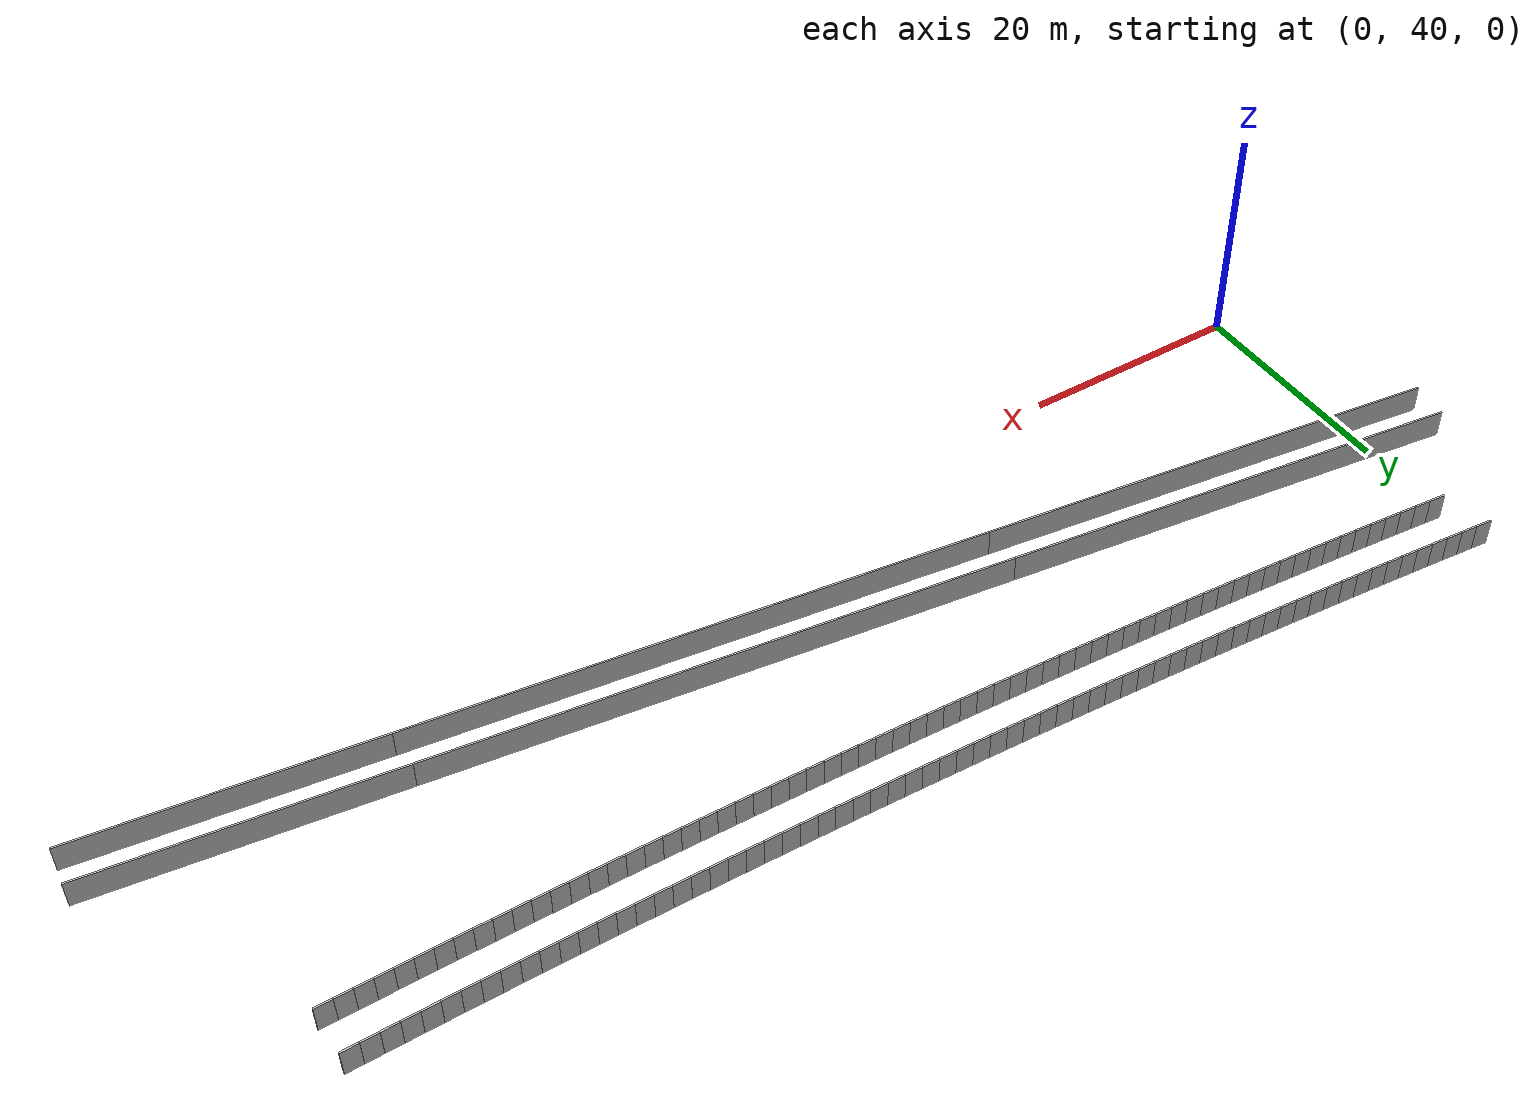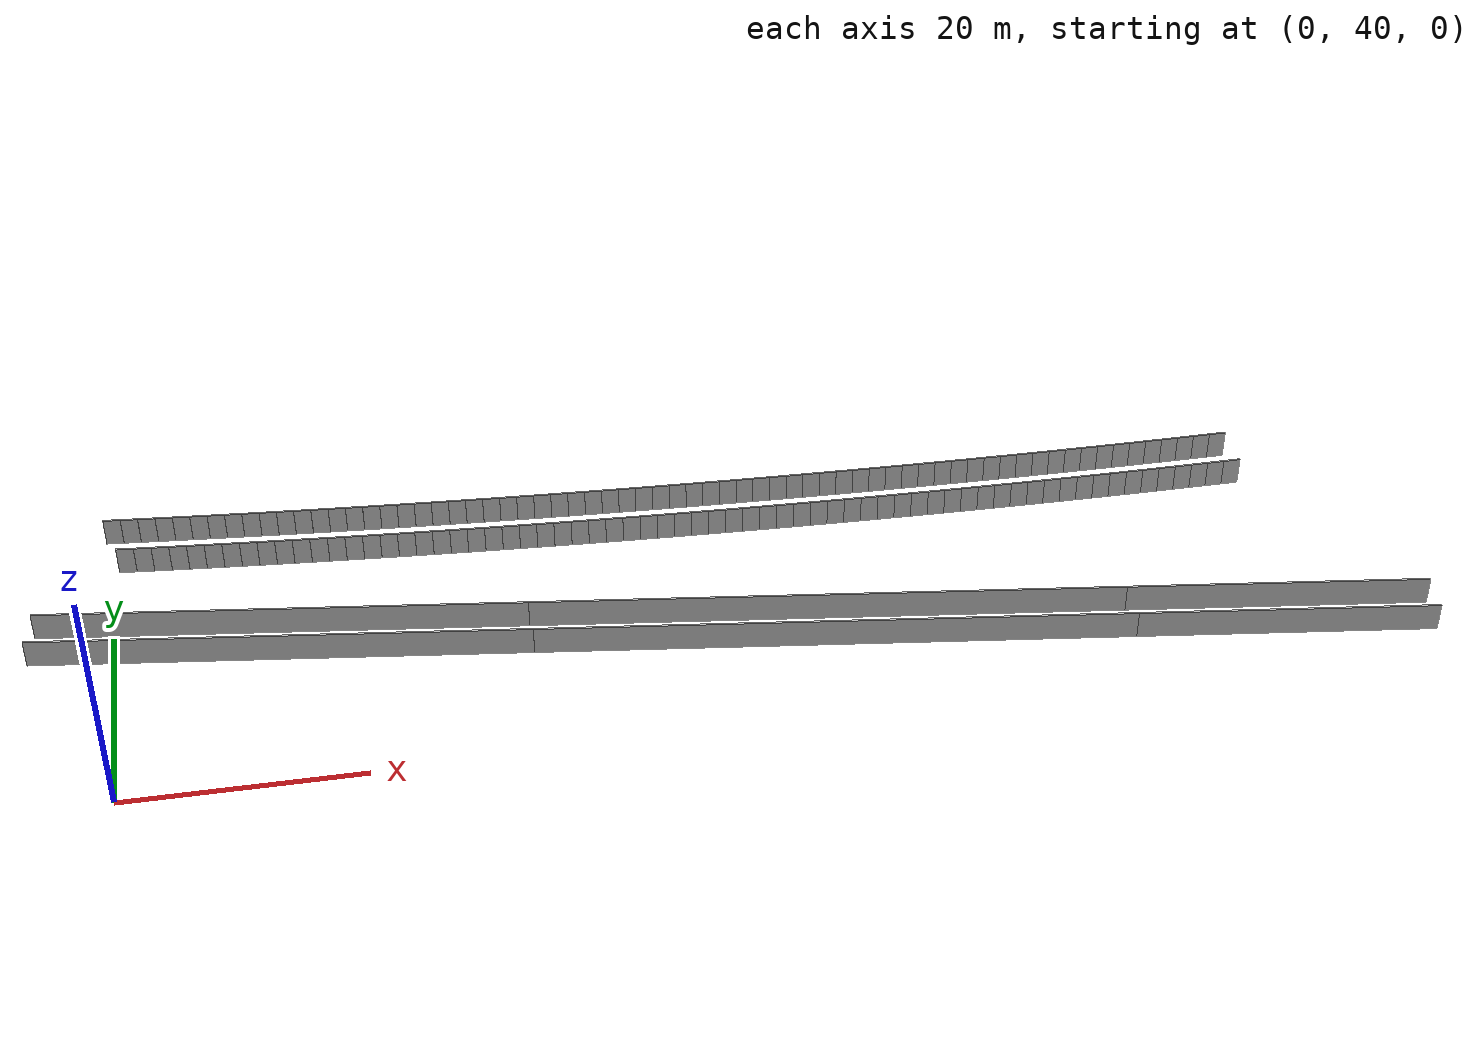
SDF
<?xml version="1.0" ?>
<sdf version="1.6">
  <model name="sps_1201">
    <pose frame="">0 0 0 0 -0 0</pose>
    <static>1</static>
    <self_collide>0</self_collide>
    <allow_auto_disable>0</allow_auto_disable>
    <link name="Wall303">
      <kinematic>0</kinematic>
      <gravity>1</gravity>
      <self_collide>0</self_collide>
      <collision name="collision">
        <geometry>
          <box>
            <size>25.4413 0.15 2.5</size>
          </box>
        </geometry>
        <pose frame="">0 0 0 0 -0 0</pose>
      </collision>
      <visual name="visual">
        <geometry>
          <box>
            <size>25.4413 0.15 2.5</size>
          </box>
        </geometry>
        <pose frame="">0 0 0 0 -0 0</pose>
        <cast_shadows>1</cast_shadows>
        <transparency>0.0</transparency>
      </visual>
      <pose frame="">97.077 44.005 1.25 0 -0 3.00818</pose>
    </link>
    <link name="Wall304">
      <kinematic>0</kinematic>
      <gravity>1</gravity>
      <self_collide>0</self_collide>
      <collision name="collision">
        <geometry>
          <box>
            <size>50.4483 0.15 2.5</size>
          </box>
        </geometry>
        <pose frame="">0 0 0 0 -0 0</pose>
      </collision>
      <visual name="visual">
        <geometry>
          <box>
            <size>50.4483 0.15 2.5</size>
          </box>
        </geometry>
        <pose frame="">0 0 0 0 -0 0</pose>
        <cast_shadows>1</cast_shadows>
        <transparency>0.0</transparency>
      </visual>
      <pose frame="">59.4694 49.0525 1.25 0 -0 3.00818</pose>
    </link>
    <link name="Wall305">
      <kinematic>0</kinematic>
      <gravity>1</gravity>
      <self_collide>0</self_collide>
      <collision name="collision">
        <geometry>
          <box>
            <size>41.997 0.15 2.5</size>
          </box>
        </geometry>
        <pose frame="">0 0 0 0 -0 0</pose>
      </collision>
      <visual name="visual">
        <geometry>
          <box>
            <size>41.997 0.15 2.5</size>
          </box>
        </geometry>
        <pose frame="">0 0 0 0 -0 0</pose>
        <cast_shadows>1</cast_shadows>
        <transparency>0.0</transparency>
      </visual>
      <pose frame="">13.6576 55.201 1.25 0 -0 3.00818</pose>
    </link>
    <link name="Wall559">
      <kinematic>0</kinematic>
      <gravity>1</gravity>
      <self_collide>0</self_collide>
      <collision name="collision">
        <geometry>
          <box>
            <size>41.4314 0.15 2.5</size>
          </box>
        </geometry>
        <pose frame="">0 0 0 0 -0 0</pose>
      </collision>
      <visual name="visual">
        <geometry>
          <box>
            <size>41.4314 0.15 2.5</size>
          </box>
        </geometry>
        <pose frame="">0 0 0 0 -0 0</pose>
        <cast_shadows>1</cast_shadows>
        <transparency>0.0</transparency>
      </visual>
      <pose frame="">13.9379 58.6946 1.25 0 0 -0.133417</pose>
    </link>
    <link name="Wall560">
      <kinematic>0</kinematic>
      <gravity>1</gravity>
      <self_collide>0</self_collide>
      <collision name="collision">
        <geometry>
          <box>
            <size>50.4483 0.15 2.5</size>
          </box>
        </geometry>
        <pose frame="">0 0 0 0 -0 0</pose>
      </collision>
      <visual name="visual">
        <geometry>
          <box>
            <size>50.4483 0.15 2.5</size>
          </box>
        </geometry>
        <pose frame="">0 0 0 0 -0 0</pose>
        <cast_shadows>1</cast_shadows>
        <transparency>0.0</transparency>
      </visual>
      <pose frame="">59.4694 52.5837 1.25 0 0 -0.133417</pose>
    </link>
    <link name="Wall561">
      <kinematic>0</kinematic>
      <gravity>1</gravity>
      <self_collide>0</self_collide>
      <collision name="collision">
        <geometry>
          <box>
            <size>25.8198 0.15 2.5</size>
          </box>
        </geometry>
        <pose frame="">0 0 0 0 -0 0</pose>
      </collision>
      <visual name="visual">
        <geometry>
          <box>
            <size>25.8198 0.15 2.5</size>
          </box>
        </geometry>
        <pose frame="">0 0 0 0 -0 0</pose>
        <cast_shadows>1</cast_shadows>
        <transparency>0.0</transparency>
      </visual>
      <pose frame="">97.2646 47.511 1.25 0 0 -0.133417</pose>
    </link>
    <link name="Wall3644">
      <kinematic>0</kinematic>
      <gravity>1</gravity>
      <self_collide>0</self_collide>
      <collision name="collision">
        <geometry>
          <box>
            <size>1.49647 0.15 2.5</size>
          </box>
        </geometry>
        <pose frame="">0 0 0 0 -0 0</pose>
      </collision>
      <visual name="visual">
        <geometry>
          <box>
            <size>1.49647 0.15 2.5</size>
          </box>
        </geometry>
        <pose frame="">0 0 0 0 -0 0</pose>
        <cast_shadows>1</cast_shadows>
        <transparency>0.0</transparency>
      </visual>
      <pose frame="">0.0590432 73.3704 1.25 0 0 -0.0957077</pose>
    </link>
    <link name="Wall3645">
      <kinematic>0</kinematic>
      <gravity>1</gravity>
      <self_collide>0</self_collide>
      <collision name="collision">
        <geometry>
          <box>
            <size>1.49661 0.15 2.5</size>
          </box>
        </geometry>
        <pose frame="">0 0 0 0 -0 0</pose>
      </collision>
      <visual name="visual">
        <geometry>
          <box>
            <size>1.49661 0.15 2.5</size>
          </box>
        </geometry>
        <pose frame="">0 0 0 0 -0 0</pose>
        <cast_shadows>1</cast_shadows>
        <transparency>0.0</transparency>
      </visual>
      <pose frame="">1.54885 73.2286 1.25 0 0 -0.0941011</pose>
    </link>
    <link name="Wall3646">
      <kinematic>0</kinematic>
      <gravity>1</gravity>
      <self_collide>0</self_collide>
      <collision name="collision">
        <geometry>
          <box>
            <size>1.4964 0.15 2.5</size>
          </box>
        </geometry>
        <pose frame="">0 0 0 0 -0 0</pose>
      </collision>
      <visual name="visual">
        <geometry>
          <box>
            <size>1.4964 0.15 2.5</size>
          </box>
        </geometry>
        <pose frame="">0 0 0 0 -0 0</pose>
        <cast_shadows>1</cast_shadows>
        <transparency>0.0</transparency>
      </visual>
      <pose frame="">3.03884 73.0891 1.25 0 0 -0.0925986</pose>
    </link>
    <link name="Wall3647">
      <kinematic>0</kinematic>
      <gravity>1</gravity>
      <self_collide>0</self_collide>
      <collision name="collision">
        <geometry>
          <box>
            <size>1.49661 0.15 2.5</size>
          </box>
        </geometry>
        <pose frame="">0 0 0 0 -0 0</pose>
      </collision>
      <visual name="visual">
        <geometry>
          <box>
            <size>1.49661 0.15 2.5</size>
          </box>
        </geometry>
        <pose frame="">0 0 0 0 -0 0</pose>
        <cast_shadows>1</cast_shadows>
        <transparency>0.0</transparency>
      </visual>
      <pose frame="">4.52904 72.9519 1.25 0 0 -0.0910291</pose>
    </link>
    <link name="Wall3648">
      <kinematic>0</kinematic>
      <gravity>1</gravity>
      <self_collide>0</self_collide>
      <collision name="collision">
        <geometry>
          <box>
            <size>1.49655 0.15 2.5</size>
          </box>
        </geometry>
        <pose frame="">0 0 0 0 -0 0</pose>
      </collision>
      <visual name="visual">
        <geometry>
          <box>
            <size>1.49655 0.15 2.5</size>
          </box>
        </geometry>
        <pose frame="">0 0 0 0 -0 0</pose>
        <cast_shadows>1</cast_shadows>
        <transparency>0.0</transparency>
      </visual>
      <pose frame="">6.01955 72.8172 1.25 0 0 -0.0892309</pose>
    </link>
    <link name="Wall3649">
      <kinematic>0</kinematic>
      <gravity>1</gravity>
      <self_collide>0</self_collide>
      <collision name="collision">
        <geometry>
          <box>
            <size>1.49655 0.15 2.5</size>
          </box>
        </geometry>
        <pose frame="">0 0 0 0 -0 0</pose>
      </collision>
      <visual name="visual">
        <geometry>
          <box>
            <size>1.49655 0.15 2.5</size>
          </box>
        </geometry>
        <pose frame="">0 0 0 0 -0 0</pose>
        <cast_shadows>1</cast_shadows>
        <transparency>0.0</transparency>
      </visual>
      <pose frame="">7.51025 72.6849 1.25 0 0 -0.0877983</pose>
    </link>
    <link name="Wall3650">
      <kinematic>0</kinematic>
      <gravity>1</gravity>
      <self_collide>0</self_collide>
      <collision name="collision">
        <geometry>
          <box>
            <size>1.49659 0.15 2.5</size>
          </box>
        </geometry>
        <pose frame="">0 0 0 0 -0 0</pose>
      </collision>
      <visual name="visual">
        <geometry>
          <box>
            <size>1.49659 0.15 2.5</size>
          </box>
        </geometry>
        <pose frame="">0 0 0 0 -0 0</pose>
        <cast_shadows>1</cast_shadows>
        <transparency>0.0</transparency>
      </visual>
      <pose frame="">9.00115 72.5548 1.25 0 0 -0.0862808</pose>
    </link>
    <link name="Wall3651">
      <kinematic>0</kinematic>
      <gravity>1</gravity>
      <self_collide>0</self_collide>
      <collision name="collision">
        <geometry>
          <box>
            <size>1.49632 0.15 2.5</size>
          </box>
        </geometry>
        <pose frame="">0 0 0 0 -0 0</pose>
      </collision>
      <visual name="visual">
        <geometry>
          <box>
            <size>1.49632 0.15 2.5</size>
          </box>
        </geometry>
        <pose frame="">0 0 0 0 -0 0</pose>
        <cast_shadows>1</cast_shadows>
        <transparency>0.0</transparency>
      </visual>
      <pose frame="">10.4921 72.4271 1.25 0 0 -0.0845775</pose>
    </link>
    <link name="Wall3652">
      <kinematic>0</kinematic>
      <gravity>1</gravity>
      <self_collide>0</self_collide>
      <collision name="collision">
        <geometry>
          <box>
            <size>1.49656 0.15 2.5</size>
          </box>
        </geometry>
        <pose frame="">0 0 0 0 -0 0</pose>
      </collision>
      <visual name="visual">
        <geometry>
          <box>
            <size>1.49656 0.15 2.5</size>
          </box>
        </geometry>
        <pose frame="">0 0 0 0 -0 0</pose>
        <cast_shadows>1</cast_shadows>
        <transparency>0.0</transparency>
      </visual>
      <pose frame="">11.9833 72.3018 1.25 0 0 -0.0830904</pose>
    </link>
    <link name="Wall3653">
      <kinematic>0</kinematic>
      <gravity>1</gravity>
      <self_collide>0</self_collide>
      <collision name="collision">
        <geometry>
          <box>
            <size>1.4966 0.15 2.5</size>
          </box>
        </geometry>
        <pose frame="">0 0 0 0 -0 0</pose>
      </collision>
      <visual name="visual">
        <geometry>
          <box>
            <size>1.4966 0.15 2.5</size>
          </box>
        </geometry>
        <pose frame="">0 0 0 0 -0 0</pose>
        <cast_shadows>1</cast_shadows>
        <transparency>0.0</transparency>
      </visual>
      <pose frame="">13.4748 72.1788 1.25 0 0 -0.0814919</pose>
    </link>
    <link name="Wall3654">
      <kinematic>0</kinematic>
      <gravity>1</gravity>
      <self_collide>0</self_collide>
      <collision name="collision">
        <geometry>
          <box>
            <size>1.49633 0.15 2.5</size>
          </box>
        </geometry>
        <pose frame="">0 0 0 0 -0 0</pose>
      </collision>
      <visual name="visual">
        <geometry>
          <box>
            <size>1.49633 0.15 2.5</size>
          </box>
        </geometry>
        <pose frame="">0 0 0 0 -0 0</pose>
        <cast_shadows>1</cast_shadows>
        <transparency>0.0</transparency>
      </visual>
      <pose frame="">14.9665 72.0583 1.25 0 0 -0.079747</pose>
    </link>
    <link name="Wall3655">
      <kinematic>0</kinematic>
      <gravity>1</gravity>
      <self_collide>0</self_collide>
      <collision name="collision">
        <geometry>
          <box>
            <size>1.4966 0.15 2.5</size>
          </box>
        </geometry>
        <pose frame="">0 0 0 0 -0 0</pose>
      </collision>
      <visual name="visual">
        <geometry>
          <box>
            <size>1.4966 0.15 2.5</size>
          </box>
        </geometry>
        <pose frame="">0 0 0 0 -0 0</pose>
        <cast_shadows>1</cast_shadows>
        <transparency>0.0</transparency>
      </visual>
      <pose frame="">16.4582 71.9401 1.25 0 0 -0.0783827</pose>
    </link>
    <link name="Wall3656">
      <kinematic>0</kinematic>
      <gravity>1</gravity>
      <self_collide>0</self_collide>
      <collision name="collision">
        <geometry>
          <box>
            <size>1.4966 0.15 2.5</size>
          </box>
        </geometry>
        <pose frame="">0 0 0 0 -0 0</pose>
      </collision>
      <visual name="visual">
        <geometry>
          <box>
            <size>1.4966 0.15 2.5</size>
          </box>
        </geometry>
        <pose frame="">0 0 0 0 -0 0</pose>
        <cast_shadows>1</cast_shadows>
        <transparency>0.0</transparency>
      </visual>
      <pose frame="">17.9503 71.8241 1.25 0 0 -0.0767875</pose>
    </link>
    <link name="Wall3657">
      <kinematic>0</kinematic>
      <gravity>1</gravity>
      <self_collide>0</self_collide>
      <collision name="collision">
        <geometry>
          <box>
            <size>1.49646 0.15 2.5</size>
          </box>
        </geometry>
        <pose frame="">0 0 0 0 -0 0</pose>
      </collision>
      <visual name="visual">
        <geometry>
          <box>
            <size>1.49646 0.15 2.5</size>
          </box>
        </geometry>
        <pose frame="">0 0 0 0 -0 0</pose>
        <cast_shadows>1</cast_shadows>
        <transparency>0.0</transparency>
      </visual>
      <pose frame="">19.4426 71.7106 1.25 0 0 -0.0750358</pose>
    </link>
    <link name="Wall3658">
      <kinematic>0</kinematic>
      <gravity>1</gravity>
      <self_collide>0</self_collide>
      <collision name="collision">
        <geometry>
          <box>
            <size>1.4966 0.15 2.5</size>
          </box>
        </geometry>
        <pose frame="">0 0 0 0 -0 0</pose>
      </collision>
      <visual name="visual">
        <geometry>
          <box>
            <size>1.4966 0.15 2.5</size>
          </box>
        </geometry>
        <pose frame="">0 0 0 0 -0 0</pose>
        <cast_shadows>1</cast_shadows>
        <transparency>0.0</transparency>
      </visual>
      <pose frame="">20.935 71.5995 1.25 0 0 -0.0735564</pose>
    </link>
    <link name="Wall3659">
      <kinematic>0</kinematic>
      <gravity>1</gravity>
      <self_collide>0</self_collide>
      <collision name="collision">
        <geometry>
          <box>
            <size>1.49648 0.15 2.5</size>
          </box>
        </geometry>
        <pose frame="">0 0 0 0 -0 0</pose>
      </collision>
      <visual name="visual">
        <geometry>
          <box>
            <size>1.49648 0.15 2.5</size>
          </box>
        </geometry>
        <pose frame="">0 0 0 0 -0 0</pose>
        <cast_shadows>1</cast_shadows>
        <transparency>0.0</transparency>
      </visual>
      <pose frame="">22.4275 71.4908 1.25 0 0 -0.0718451</pose>
    </link>
    <link name="Wall3660">
      <kinematic>0</kinematic>
      <gravity>1</gravity>
      <self_collide>0</self_collide>
      <collision name="collision">
        <geometry>
          <box>
            <size>1.4965 0.15 2.5</size>
          </box>
        </geometry>
        <pose frame="">0 0 0 0 -0 0</pose>
      </collision>
      <visual name="visual">
        <geometry>
          <box>
            <size>1.4965 0.15 2.5</size>
          </box>
        </geometry>
        <pose frame="">0 0 0 0 -0 0</pose>
        <cast_shadows>1</cast_shadows>
        <transparency>0.0</transparency>
      </visual>
      <pose frame="">23.9202 71.3845 1.25 0 0 -0.0703718</pose>
    </link>
    <link name="Wall3661">
      <kinematic>0</kinematic>
      <gravity>1</gravity>
      <self_collide>0</self_collide>
      <collision name="collision">
        <geometry>
          <box>
            <size>1.49653 0.15 2.5</size>
          </box>
        </geometry>
        <pose frame="">0 0 0 0 -0 0</pose>
      </collision>
      <visual name="visual">
        <geometry>
          <box>
            <size>1.49653 0.15 2.5</size>
          </box>
        </geometry>
        <pose frame="">0 0 0 0 -0 0</pose>
        <cast_shadows>1</cast_shadows>
        <transparency>0.0</transparency>
      </visual>
      <pose frame="">25.4131 71.2804 1.25 0 0 -0.0688579</pose>
    </link>
    <link name="Wall3662">
      <kinematic>0</kinematic>
      <gravity>1</gravity>
      <self_collide>0</self_collide>
      <collision name="collision">
        <geometry>
          <box>
            <size>1.49641 0.15 2.5</size>
          </box>
        </geometry>
        <pose frame="">0 0 0 0 -0 0</pose>
      </collision>
      <visual name="visual">
        <geometry>
          <box>
            <size>1.49641 0.15 2.5</size>
          </box>
        </geometry>
        <pose frame="">0 0 0 0 -0 0</pose>
        <cast_shadows>1</cast_shadows>
        <transparency>0.0</transparency>
      </visual>
      <pose frame="">26.9062 71.1787 1.25 0 0 -0.0671461</pose>
    </link>
    <link name="Wall3663">
      <kinematic>0</kinematic>
      <gravity>1</gravity>
      <self_collide>0</self_collide>
      <collision name="collision">
        <geometry>
          <box>
            <size>1.49663 0.15 2.5</size>
          </box>
        </geometry>
        <pose frame="">0 0 0 0 -0 0</pose>
      </collision>
      <visual name="visual">
        <geometry>
          <box>
            <size>1.49663 0.15 2.5</size>
          </box>
        </geometry>
        <pose frame="">0 0 0 0 -0 0</pose>
        <cast_shadows>1</cast_shadows>
        <transparency>0.0</transparency>
      </visual>
      <pose frame="">28.3994 71.0794 1.25 0 0 -0.0656648</pose>
    </link>
    <link name="Wall3664">
      <kinematic>0</kinematic>
      <gravity>1</gravity>
      <self_collide>0</self_collide>
      <collision name="collision">
        <geometry>
          <box>
            <size>1.49642 0.15 2.5</size>
          </box>
        </geometry>
        <pose frame="">0 0 0 0 -0 0</pose>
      </collision>
      <visual name="visual">
        <geometry>
          <box>
            <size>1.49642 0.15 2.5</size>
          </box>
        </geometry>
        <pose frame="">0 0 0 0 -0 0</pose>
        <cast_shadows>1</cast_shadows>
        <transparency>0.0</transparency>
      </visual>
      <pose frame="">29.8928 70.9824 1.25 0 0 -0.0640802</pose>
    </link>
    <link name="Wall3665">
      <kinematic>0</kinematic>
      <gravity>1</gravity>
      <self_collide>0</self_collide>
      <collision name="collision">
        <geometry>
          <box>
            <size>1.49657 0.15 2.5</size>
          </box>
        </geometry>
        <pose frame="">0 0 0 0 -0 0</pose>
      </collision>
      <visual name="visual">
        <geometry>
          <box>
            <size>1.49657 0.15 2.5</size>
          </box>
        </geometry>
        <pose frame="">0 0 0 0 -0 0</pose>
        <cast_shadows>1</cast_shadows>
        <transparency>0.0</transparency>
      </visual>
      <pose frame="">31.3863 70.8878 1.25 0 0 -0.0624392</pose>
    </link>
    <link name="Wall3666">
      <kinematic>0</kinematic>
      <gravity>1</gravity>
      <self_collide>0</self_collide>
      <collision name="collision">
        <geometry>
          <box>
            <size>1.49654 0.15 2.5</size>
          </box>
        </geometry>
        <pose frame="">0 0 0 0 -0 0</pose>
      </collision>
      <visual name="visual">
        <geometry>
          <box>
            <size>1.49654 0.15 2.5</size>
          </box>
        </geometry>
        <pose frame="">0 0 0 0 -0 0</pose>
        <cast_shadows>1</cast_shadows>
        <transparency>0.0</transparency>
      </visual>
      <pose frame="">32.88 70.7956 1.25 0 0 -0.0608466</pose>
    </link>
    <link name="Wall3667">
      <kinematic>0</kinematic>
      <gravity>1</gravity>
      <self_collide>0</self_collide>
      <collision name="collision">
        <geometry>
          <box>
            <size>1.49641 0.15 2.5</size>
          </box>
        </geometry>
        <pose frame="">0 0 0 0 -0 0</pose>
      </collision>
      <visual name="visual">
        <geometry>
          <box>
            <size>1.49641 0.15 2.5</size>
          </box>
        </geometry>
        <pose frame="">0 0 0 0 -0 0</pose>
        <cast_shadows>1</cast_shadows>
        <transparency>0.0</transparency>
      </visual>
      <pose frame="">34.3737 70.7057 1.25 0 0 -0.059381</pose>
    </link>
    <link name="Wall3668">
      <kinematic>0</kinematic>
      <gravity>1</gravity>
      <self_collide>0</self_collide>
      <collision name="collision">
        <geometry>
          <box>
            <size>1.49668 0.15 2.5</size>
          </box>
        </geometry>
        <pose frame="">0 0 0 0 -0 0</pose>
      </collision>
      <visual name="visual">
        <geometry>
          <box>
            <size>1.49668 0.15 2.5</size>
          </box>
        </geometry>
        <pose frame="">0 0 0 0 -0 0</pose>
        <cast_shadows>1</cast_shadows>
        <transparency>0.0</transparency>
      </visual>
      <pose frame="">35.8677 70.6182 1.25 0 0 -0.0576136</pose>
    </link>
    <link name="Wall3669">
      <kinematic>0</kinematic>
      <gravity>1</gravity>
      <self_collide>0</self_collide>
      <collision name="collision">
        <geometry>
          <box>
            <size>1.49638 0.15 2.5</size>
          </box>
        </geometry>
        <pose frame="">0 0 0 0 -0 0</pose>
      </collision>
      <visual name="visual">
        <geometry>
          <box>
            <size>1.49638 0.15 2.5</size>
          </box>
        </geometry>
        <pose frame="">0 0 0 0 -0 0</pose>
        <cast_shadows>1</cast_shadows>
        <transparency>0.0</transparency>
      </visual>
      <pose frame="">37.3618 70.5331 1.25 0 0 -0.0561546</pose>
    </link>
    <link name="Wall3670">
      <kinematic>0</kinematic>
      <gravity>1</gravity>
      <self_collide>0</self_collide>
      <collision name="collision">
        <geometry>
          <box>
            <size>1.49661 0.15 2.5</size>
          </box>
        </geometry>
        <pose frame="">0 0 0 0 -0 0</pose>
      </collision>
      <visual name="visual">
        <geometry>
          <box>
            <size>1.49661 0.15 2.5</size>
          </box>
        </geometry>
        <pose frame="">0 0 0 0 -0 0</pose>
        <cast_shadows>1</cast_shadows>
        <transparency>0.0</transparency>
      </visual>
      <pose frame="">38.856 70.4503 1.25 0 0 -0.0545529</pose>
    </link>
    <link name="Wall3671">
      <kinematic>0</kinematic>
      <gravity>1</gravity>
      <self_collide>0</self_collide>
      <collision name="collision">
        <geometry>
          <box>
            <size>1.49654 0.15 2.5</size>
          </box>
        </geometry>
        <pose frame="">0 0 0 0 -0 0</pose>
      </collision>
      <visual name="visual">
        <geometry>
          <box>
            <size>1.49654 0.15 2.5</size>
          </box>
        </geometry>
        <pose frame="">0 0 0 0 -0 0</pose>
        <cast_shadows>1</cast_shadows>
        <transparency>0.0</transparency>
      </visual>
      <pose frame="">40.3505 70.3699 1.25 0 0 -0.0529625</pose>
    </link>
    <link name="Wall3672">
      <kinematic>0</kinematic>
      <gravity>1</gravity>
      <self_collide>0</self_collide>
      <collision name="collision">
        <geometry>
          <box>
            <size>1.49653 0.15 2.5</size>
          </box>
        </geometry>
        <pose frame="">0 0 0 0 -0 0</pose>
      </collision>
      <visual name="visual">
        <geometry>
          <box>
            <size>1.49653 0.15 2.5</size>
          </box>
        </geometry>
        <pose frame="">0 0 0 0 -0 0</pose>
        <cast_shadows>1</cast_shadows>
        <transparency>0.0</transparency>
      </visual>
      <pose frame="">41.845 70.292 1.25 0 0 -0.0512069</pose>
    </link>
    <link name="Wall3673">
      <kinematic>0</kinematic>
      <gravity>1</gravity>
      <self_collide>0</self_collide>
      <collision name="collision">
        <geometry>
          <box>
            <size>1.49649 0.15 2.5</size>
          </box>
        </geometry>
        <pose frame="">0 0 0 0 -0 0</pose>
      </collision>
      <visual name="visual">
        <geometry>
          <box>
            <size>1.49649 0.15 2.5</size>
          </box>
        </geometry>
        <pose frame="">0 0 0 0 -0 0</pose>
        <cast_shadows>1</cast_shadows>
        <transparency>0.0</transparency>
      </visual>
      <pose frame="">43.3396 70.2164 1.25 0 0 -0.0498606</pose>
    </link>
    <link name="Wall3674">
      <kinematic>0</kinematic>
      <gravity>1</gravity>
      <self_collide>0</self_collide>
      <collision name="collision">
        <geometry>
          <box>
            <size>1.49649 0.15 2.5</size>
          </box>
        </geometry>
        <pose frame="">0 0 0 0 -0 0</pose>
      </collision>
      <visual name="visual">
        <geometry>
          <box>
            <size>1.49649 0.15 2.5</size>
          </box>
        </geometry>
        <pose frame="">0 0 0 0 -0 0</pose>
        <cast_shadows>1</cast_shadows>
        <transparency>0.0</transparency>
      </visual>
      <pose frame="">44.8343 70.1431 1.25 0 0 -0.0481457</pose>
    </link>
    <link name="Wall3675">
      <kinematic>0</kinematic>
      <gravity>1</gravity>
      <self_collide>0</self_collide>
      <collision name="collision">
        <geometry>
          <box>
            <size>1.49667 0.15 2.5</size>
          </box>
        </geometry>
        <pose frame="">0 0 0 0 -0 0</pose>
      </collision>
      <visual name="visual">
        <geometry>
          <box>
            <size>1.49667 0.15 2.5</size>
          </box>
        </geometry>
        <pose frame="">0 0 0 0 -0 0</pose>
        <cast_shadows>1</cast_shadows>
        <transparency>0.0</transparency>
      </visual>
      <pose frame="">46.3292 70.0723 1.25 0 0 -0.0465066</pose>
    </link>
    <link name="Wall3676">
      <kinematic>0</kinematic>
      <gravity>1</gravity>
      <self_collide>0</self_collide>
      <collision name="collision">
        <geometry>
          <box>
            <size>1.49651 0.15 2.5</size>
          </box>
        </geometry>
        <pose frame="">0 0 0 0 -0 0</pose>
      </collision>
      <visual name="visual">
        <geometry>
          <box>
            <size>1.49651 0.15 2.5</size>
          </box>
        </geometry>
        <pose frame="">0 0 0 0 -0 0</pose>
        <cast_shadows>1</cast_shadows>
        <transparency>0.0</transparency>
      </visual>
      <pose frame="">47.8242 70.0038 1.25 0 0 -0.0450418</pose>
    </link>
    <link name="Wall3677">
      <kinematic>0</kinematic>
      <gravity>1</gravity>
      <self_collide>0</self_collide>
      <collision name="collision">
        <geometry>
          <box>
            <size>1.49659 0.15 2.5</size>
          </box>
        </geometry>
        <pose frame="">0 0 0 0 -0 0</pose>
      </collision>
      <visual name="visual">
        <geometry>
          <box>
            <size>1.49659 0.15 2.5</size>
          </box>
        </geometry>
        <pose frame="">0 0 0 0 -0 0</pose>
        <cast_shadows>1</cast_shadows>
        <transparency>0.0</transparency>
      </visual>
      <pose frame="">49.3193 69.9376 1.25 0 0 -0.0434474</pose>
    </link>
    <link name="Wall3678">
      <kinematic>0</kinematic>
      <gravity>1</gravity>
      <self_collide>0</self_collide>
      <collision name="collision">
        <geometry>
          <box>
            <size>1.49649 0.15 2.5</size>
          </box>
        </geometry>
        <pose frame="">0 0 0 0 -0 0</pose>
      </collision>
      <visual name="visual">
        <geometry>
          <box>
            <size>1.49649 0.15 2.5</size>
          </box>
        </geometry>
        <pose frame="">0 0 0 0 -0 0</pose>
        <cast_shadows>1</cast_shadows>
        <transparency>0.0</transparency>
      </visual>
      <pose frame="">50.8144 69.8738 1.25 0 0 -0.0418582</pose>
    </link>
    <link name="Wall3679">
      <kinematic>0</kinematic>
      <gravity>1</gravity>
      <self_collide>0</self_collide>
      <collision name="collision">
        <geometry>
          <box>
            <size>1.49645 0.15 2.5</size>
          </box>
        </geometry>
        <pose frame="">0 0 0 0 -0 0</pose>
      </collision>
      <visual name="visual">
        <geometry>
          <box>
            <size>1.49645 0.15 2.5</size>
          </box>
        </geometry>
        <pose frame="">0 0 0 0 -0 0</pose>
        <cast_shadows>1</cast_shadows>
        <transparency>0.0</transparency>
      </visual>
      <pose frame="">52.3097 69.8124 1.25 0 0 -0.0402265</pose>
    </link>
    <link name="Wall3680">
      <kinematic>0</kinematic>
      <gravity>1</gravity>
      <self_collide>0</self_collide>
      <collision name="collision">
        <geometry>
          <box>
            <size>1.49649 0.15 2.5</size>
          </box>
        </geometry>
        <pose frame="">0 0 0 0 -0 0</pose>
      </collision>
      <visual name="visual">
        <geometry>
          <box>
            <size>1.49649 0.15 2.5</size>
          </box>
        </geometry>
        <pose frame="">0 0 0 0 -0 0</pose>
        <cast_shadows>1</cast_shadows>
        <transparency>0.0</transparency>
      </visual>
      <pose frame="">53.805 69.7533 1.25 0 0 -0.0387561</pose>
    </link>
    <link name="Wall3681">
      <kinematic>0</kinematic>
      <gravity>1</gravity>
      <self_collide>0</self_collide>
      <collision name="collision">
        <geometry>
          <box>
            <size>1.49663 0.15 2.5</size>
          </box>
        </geometry>
        <pose frame="">0 0 0 0 -0 0</pose>
      </collision>
      <visual name="visual">
        <geometry>
          <box>
            <size>1.49663 0.15 2.5</size>
          </box>
        </geometry>
        <pose frame="">0 0 0 0 -0 0</pose>
        <cast_shadows>1</cast_shadows>
        <transparency>0.0</transparency>
      </visual>
      <pose frame="">55.3004 69.6966 1.25 0 0 -0.0370382</pose>
    </link>
    <link name="Wall3682">
      <kinematic>0</kinematic>
      <gravity>1</gravity>
      <self_collide>0</self_collide>
      <collision name="collision">
        <geometry>
          <box>
            <size>1.49655 0.15 2.5</size>
          </box>
        </geometry>
        <pose frame="">0 0 0 0 -0 0</pose>
      </collision>
      <visual name="visual">
        <geometry>
          <box>
            <size>1.49655 0.15 2.5</size>
          </box>
        </geometry>
        <pose frame="">0 0 0 0 -0 0</pose>
        <cast_shadows>1</cast_shadows>
        <transparency>0.0</transparency>
      </visual>
      <pose frame="">56.796 69.6423 1.25 0 0 -0.035571</pose>
    </link>
    <link name="Wall3683">
      <kinematic>0</kinematic>
      <gravity>1</gravity>
      <self_collide>0</self_collide>
      <collision name="collision">
        <geometry>
          <box>
            <size>1.49647 0.15 2.5</size>
          </box>
        </geometry>
        <pose frame="">0 0 0 0 -0 0</pose>
      </collision>
      <visual name="visual">
        <geometry>
          <box>
            <size>1.49647 0.15 2.5</size>
          </box>
        </geometry>
        <pose frame="">0 0 0 0 -0 0</pose>
        <cast_shadows>1</cast_shadows>
        <transparency>0.0</transparency>
      </visual>
      <pose frame="">58.2916 69.5903 1.25 0 0 -0.0339406</pose>
    </link>
    <link name="Wall3684">
      <kinematic>0</kinematic>
      <gravity>1</gravity>
      <self_collide>0</self_collide>
      <collision name="collision">
        <geometry>
          <box>
            <size>1.49657 0.15 2.5</size>
          </box>
        </geometry>
        <pose frame="">0 0 0 0 -0 0</pose>
      </collision>
      <visual name="visual">
        <geometry>
          <box>
            <size>1.49657 0.15 2.5</size>
          </box>
        </geometry>
        <pose frame="">0 0 0 0 -0 0</pose>
        <cast_shadows>1</cast_shadows>
        <transparency>0.0</transparency>
      </visual>
      <pose frame="">59.7873 69.5407 1.25 0 0 -0.0323468</pose>
    </link>
    <link name="Wall3685">
      <kinematic>0</kinematic>
      <gravity>1</gravity>
      <self_collide>0</self_collide>
      <collision name="collision">
        <geometry>
          <box>
            <size>1.4965 0.15 2.5</size>
          </box>
        </geometry>
        <pose frame="">0 0 0 0 -0 0</pose>
      </collision>
      <visual name="visual">
        <geometry>
          <box>
            <size>1.4965 0.15 2.5</size>
          </box>
        </geometry>
        <pose frame="">0 0 0 0 -0 0</pose>
        <cast_shadows>1</cast_shadows>
        <transparency>0.0</transparency>
      </visual>
      <pose frame="">61.2831 69.4935 1.25 0 0 -0.030757</pose>
    </link>
    <link name="Wall3686">
      <kinematic>0</kinematic>
      <gravity>1</gravity>
      <self_collide>0</self_collide>
      <collision name="collision">
        <geometry>
          <box>
            <size>1.49648 0.15 2.5</size>
          </box>
        </geometry>
        <pose frame="">0 0 0 0 -0 0</pose>
      </collision>
      <visual name="visual">
        <geometry>
          <box>
            <size>1.49648 0.15 2.5</size>
          </box>
        </geometry>
        <pose frame="">0 0 0 0 -0 0</pose>
        <cast_shadows>1</cast_shadows>
        <transparency>0.0</transparency>
      </visual>
      <pose frame="">62.779 69.4487 1.25 0 0 -0.0291251</pose>
    </link>
    <link name="Wall3687">
      <kinematic>0</kinematic>
      <gravity>1</gravity>
      <self_collide>0</self_collide>
      <collision name="collision">
        <geometry>
          <box>
            <size>1.49654 0.15 2.5</size>
          </box>
        </geometry>
        <pose frame="">0 0 0 0 -0 0</pose>
      </collision>
      <visual name="visual">
        <geometry>
          <box>
            <size>1.49654 0.15 2.5</size>
          </box>
        </geometry>
        <pose frame="">0 0 0 0 -0 0</pose>
        <cast_shadows>1</cast_shadows>
        <transparency>0.0</transparency>
      </visual>
      <pose frame="">64.2749 69.4063 1.25 0 0 -0.0275328</pose>
    </link>
    <link name="Wall3688">
      <kinematic>0</kinematic>
      <gravity>1</gravity>
      <self_collide>0</self_collide>
      <collision name="collision">
        <geometry>
          <box>
            <size>1.49654 0.15 2.5</size>
          </box>
        </geometry>
        <pose frame="">0 0 0 0 -0 0</pose>
      </collision>
      <visual name="visual">
        <geometry>
          <box>
            <size>1.49654 0.15 2.5</size>
          </box>
        </geometry>
        <pose frame="">0 0 0 0 -0 0</pose>
        <cast_shadows>1</cast_shadows>
        <transparency>0.0</transparency>
      </visual>
      <pose frame="">65.7709 69.3662 1.25 0 0 -0.026064</pose>
    </link>
    <link name="Wall3689">
      <kinematic>0</kinematic>
      <gravity>1</gravity>
      <self_collide>0</self_collide>
      <collision name="collision">
        <geometry>
          <box>
            <size>1.4966 0.15 2.5</size>
          </box>
        </geometry>
        <pose frame="">0 0 0 0 -0 0</pose>
      </collision>
      <visual name="visual">
        <geometry>
          <box>
            <size>1.4966 0.15 2.5</size>
          </box>
        </geometry>
        <pose frame="">0 0 0 0 -0 0</pose>
        <cast_shadows>1</cast_shadows>
        <transparency>0.0</transparency>
      </visual>
      <pose frame="">67.267 69.3284 1.25 0 0 -0.0244719</pose>
    </link>
    <link name="Wall3690">
      <kinematic>0</kinematic>
      <gravity>1</gravity>
      <self_collide>0</self_collide>
      <collision name="collision">
        <geometry>
          <box>
            <size>1.49642 0.15 2.5</size>
          </box>
        </geometry>
        <pose frame="">0 0 0 0 -0 0</pose>
      </collision>
      <visual name="visual">
        <geometry>
          <box>
            <size>1.49642 0.15 2.5</size>
          </box>
        </geometry>
        <pose frame="">0 0 0 0 -0 0</pose>
        <cast_shadows>1</cast_shadows>
        <transparency>0.0</transparency>
      </visual>
      <pose frame="">68.7631 69.2931 1.25 0 0 -0.0227206</pose>
    </link>
    <link name="Wall3691">
      <kinematic>0</kinematic>
      <gravity>1</gravity>
      <self_collide>0</self_collide>
      <collision name="collision">
        <geometry>
          <box>
            <size>1.49655 0.15 2.5</size>
          </box>
        </geometry>
        <pose frame="">0 0 0 0 -0 0</pose>
      </collision>
      <visual name="visual">
        <geometry>
          <box>
            <size>1.49655 0.15 2.5</size>
          </box>
        </geometry>
        <pose frame="">0 0 0 0 -0 0</pose>
        <cast_shadows>1</cast_shadows>
        <transparency>0.0</transparency>
      </visual>
      <pose frame="">70.2592 69.2602 1.25 0 0 -0.02125</pose>
    </link>
    <link name="Wall3692">
      <kinematic>0</kinematic>
      <gravity>1</gravity>
      <self_collide>0</self_collide>
      <collision name="collision">
        <geometry>
          <box>
            <size>1.49645 0.15 2.5</size>
          </box>
        </geometry>
        <pose frame="">0 0 0 0 -0 0</pose>
      </collision>
      <visual name="visual">
        <geometry>
          <box>
            <size>1.49645 0.15 2.5</size>
          </box>
        </geometry>
        <pose frame="">0 0 0 0 -0 0</pose>
        <cast_shadows>1</cast_shadows>
        <transparency>0.0</transparency>
      </visual>
      <pose frame="">71.7554 69.2295 1.25 0 0 -0.0197828</pose>
    </link>
    <link name="Wall3693">
      <kinematic>0</kinematic>
      <gravity>1</gravity>
      <self_collide>0</self_collide>
      <collision name="collision">
        <geometry>
          <box>
            <size>1.49646 0.15 2.5</size>
          </box>
        </geometry>
        <pose frame="">0 0 0 0 -0 0</pose>
      </collision>
      <visual name="visual">
        <geometry>
          <box>
            <size>1.49646 0.15 2.5</size>
          </box>
        </geometry>
        <pose frame="">0 0 0 0 -0 0</pose>
        <cast_shadows>1</cast_shadows>
        <transparency>0.0</transparency>
      </visual>
      <pose frame="">73.2515 69.2012 1.25 0 0 -0.0180286</pose>
    </link>
    <link name="Wall3694">
      <kinematic>0</kinematic>
      <gravity>1</gravity>
      <self_collide>0</self_collide>
      <collision name="collision">
        <geometry>
          <box>
            <size>1.4966 0.15 2.5</size>
          </box>
        </geometry>
        <pose frame="">0 0 0 0 -0 0</pose>
      </collision>
      <visual name="visual">
        <geometry>
          <box>
            <size>1.4966 0.15 2.5</size>
          </box>
        </geometry>
        <pose frame="">0 0 0 0 -0 0</pose>
        <cast_shadows>1</cast_shadows>
        <transparency>0.0</transparency>
      </visual>
      <pose frame="">74.7479 69.1754 1.25 0 0 -0.0164361</pose>
    </link>
    <link name="Wall3695">
      <kinematic>0</kinematic>
      <gravity>1</gravity>
      <self_collide>0</self_collide>
      <collision name="collision">
        <geometry>
          <box>
            <size>1.49657 0.15 2.5</size>
          </box>
        </geometry>
        <pose frame="">0 0 0 0 -0 0</pose>
      </collision>
      <visual name="visual">
        <geometry>
          <box>
            <size>1.49657 0.15 2.5</size>
          </box>
        </geometry>
        <pose frame="">0 0 0 0 -0 0</pose>
        <cast_shadows>1</cast_shadows>
        <transparency>0.0</transparency>
      </visual>
      <pose frame="">76.2443 69.1519 1.25 0 0 -0.0149681</pose>
    </link>
    <link name="Wall3696">
      <kinematic>0</kinematic>
      <gravity>1</gravity>
      <self_collide>0</self_collide>
      <collision name="collision">
        <geometry>
          <box>
            <size>1.49653 0.15 2.5</size>
          </box>
        </geometry>
        <pose frame="">0 0 0 0 -0 0</pose>
      </collision>
      <visual name="visual">
        <geometry>
          <box>
            <size>1.49653 0.15 2.5</size>
          </box>
        </geometry>
        <pose frame="">0 0 0 0 -0 0</pose>
        <cast_shadows>1</cast_shadows>
        <transparency>0.0</transparency>
      </visual>
      <pose frame="">77.7407 69.1307 1.25 0 0 -0.0133777</pose>
    </link>
    <link name="Wall3697">
      <kinematic>0</kinematic>
      <gravity>1</gravity>
      <self_collide>0</self_collide>
      <collision name="collision">
        <geometry>
          <box>
            <size>1.49668 0.15 2.5</size>
          </box>
        </geometry>
        <pose frame="">0 0 0 0 -0 0</pose>
      </collision>
      <visual name="visual">
        <geometry>
          <box>
            <size>1.49668 0.15 2.5</size>
          </box>
        </geometry>
        <pose frame="">0 0 0 0 -0 0</pose>
        <cast_shadows>1</cast_shadows>
        <transparency>0.0</transparency>
      </visual>
      <pose frame="">79.2371 69.112 1.25 0 0 -0.0116226</pose>
    </link>
    <link name="Wall3698">
      <kinematic>0</kinematic>
      <gravity>1</gravity>
      <self_collide>0</self_collide>
      <collision name="collision">
        <geometry>
          <box>
            <size>1.49648 0.15 2.5</size>
          </box>
        </geometry>
        <pose frame="">0 0 0 0 -0 0</pose>
      </collision>
      <visual name="visual">
        <geometry>
          <box>
            <size>1.49648 0.15 2.5</size>
          </box>
        </geometry>
        <pose frame="">0 0 0 0 -0 0</pose>
        <cast_shadows>1</cast_shadows>
        <transparency>0.0</transparency>
      </visual>
      <pose frame="">80.7336 69.0957 1.25 0 0 -0.0101559</pose>
    </link>
    <link name="Wall3699">
      <kinematic>0</kinematic>
      <gravity>1</gravity>
      <self_collide>0</self_collide>
      <collision name="collision">
        <geometry>
          <box>
            <size>1.49645 0.15 2.5</size>
          </box>
        </geometry>
        <pose frame="">0 0 0 0 -0 0</pose>
      </collision>
      <visual name="visual">
        <geometry>
          <box>
            <size>1.49645 0.15 2.5</size>
          </box>
        </geometry>
        <pose frame="">0 0 0 0 -0 0</pose>
        <cast_shadows>1</cast_shadows>
        <transparency>0.0</transparency>
      </visual>
      <pose frame="">82.23 69.0817 1.25 0 0 -0.00856528</pose>
    </link>
    <link name="Wall3700">
      <kinematic>0</kinematic>
      <gravity>1</gravity>
      <self_collide>0</self_collide>
      <collision name="collision">
        <geometry>
          <box>
            <size>1.49644 0.15 2.5</size>
          </box>
        </geometry>
        <pose frame="">0 0 0 0 -0 0</pose>
      </collision>
      <visual name="visual">
        <geometry>
          <box>
            <size>1.49644 0.15 2.5</size>
          </box>
        </geometry>
        <pose frame="">0 0 0 0 -0 0</pose>
        <cast_shadows>1</cast_shadows>
        <transparency>0.0</transparency>
      </visual>
      <pose frame="">83.7264 69.07 1.25 0 0 -0.00705621</pose>
    </link>
    <link name="Wall3701">
      <kinematic>0</kinematic>
      <gravity>1</gravity>
      <self_collide>0</self_collide>
      <collision name="collision">
        <geometry>
          <box>
            <size>1.49666 0.15 2.5</size>
          </box>
        </geometry>
        <pose frame="">0 0 0 0 -0 0</pose>
      </collision>
      <visual name="visual">
        <geometry>
          <box>
            <size>1.49666 0.15 2.5</size>
          </box>
        </geometry>
        <pose frame="">0 0 0 0 -0 0</pose>
        <cast_shadows>1</cast_shadows>
        <transparency>0.0</transparency>
      </visual>
      <pose frame="">85.223 69.0607 1.25 0 0 -0.00534231</pose>
    </link>
    <link name="Wall3702">
      <kinematic>0</kinematic>
      <gravity>1</gravity>
      <self_collide>0</self_collide>
      <collision name="collision">
        <geometry>
          <box>
            <size>1.49659 0.15 2.5</size>
          </box>
        </geometry>
        <pose frame="">0 0 0 0 -0 0</pose>
      </collision>
      <visual name="visual">
        <geometry>
          <box>
            <size>1.49659 0.15 2.5</size>
          </box>
        </geometry>
        <pose frame="">0 0 0 0 -0 0</pose>
        <cast_shadows>1</cast_shadows>
        <transparency>0.0</transparency>
      </visual>
      <pose frame="">86.7196 69.0538 1.25 0 0 -0.00387437</pose>
    </link>
    <link name="Wall3703">
      <kinematic>0</kinematic>
      <gravity>1</gravity>
      <self_collide>0</self_collide>
      <collision name="collision">
        <geometry>
          <box>
            <size>1.4964 0.15 2.5</size>
          </box>
        </geometry>
        <pose frame="">0 0 0 0 -0 0</pose>
      </collision>
      <visual name="visual">
        <geometry>
          <box>
            <size>1.4964 0.15 2.5</size>
          </box>
        </geometry>
        <pose frame="">0 0 0 0 -0 0</pose>
        <cast_shadows>1</cast_shadows>
        <transparency>0.0</transparency>
      </visual>
      <pose frame="">88.2161 69.0492 1.25 0 0 -0.00228413</pose>
    </link>
    <link name="Wall3704">
      <kinematic>0</kinematic>
      <gravity>1</gravity>
      <self_collide>0</self_collide>
      <collision name="collision">
        <geometry>
          <box>
            <size>1.49658 0.15 2.5</size>
          </box>
        </geometry>
        <pose frame="">0 0 0 0 -0 0</pose>
      </collision>
      <visual name="visual">
        <geometry>
          <box>
            <size>1.49658 0.15 2.5</size>
          </box>
        </geometry>
        <pose frame="">0 0 0 0 -0 0</pose>
        <cast_shadows>1</cast_shadows>
        <transparency>0.0</transparency>
      </visual>
      <pose frame="">89.7125 69.0471 1.25 0 0 -0.000530179</pose>
    </link>
    <link name="Wall3705">
      <kinematic>0</kinematic>
      <gravity>1</gravity>
      <self_collide>0</self_collide>
      <collision name="collision">
        <geometry>
          <box>
            <size>1.49664 0.15 2.5</size>
          </box>
        </geometry>
        <pose frame="">0 0 0 0 -0 0</pose>
      </collision>
      <visual name="visual">
        <geometry>
          <box>
            <size>1.49664 0.15 2.5</size>
          </box>
        </geometry>
        <pose frame="">0 0 0 0 -0 0</pose>
        <cast_shadows>1</cast_shadows>
        <transparency>0.0</transparency>
      </visual>
      <pose frame="">91.2092 69.0474 1.25 0 -0 0.000937972</pose>
    </link>
    <link name="Wall3706">
      <kinematic>0</kinematic>
      <gravity>1</gravity>
      <self_collide>0</self_collide>
      <collision name="collision">
        <geometry>
          <box>
            <size>1.4964 0.15 2.5</size>
          </box>
        </geometry>
        <pose frame="">0 0 0 0 -0 0</pose>
      </collision>
      <visual name="visual">
        <geometry>
          <box>
            <size>1.4964 0.15 2.5</size>
          </box>
        </geometry>
        <pose frame="">0 0 0 0 -0 0</pose>
        <cast_shadows>1</cast_shadows>
        <transparency>0.0</transparency>
      </visual>
      <pose frame="">92.7057 69.0499 1.25 0 -0 0.00240649</pose>
    </link>
    <link name="Wall3707">
      <kinematic>0</kinematic>
      <gravity>1</gravity>
      <self_collide>0</self_collide>
      <collision name="collision">
        <geometry>
          <box>
            <size>1.49659 0.15 2.5</size>
          </box>
        </geometry>
        <pose frame="">0 0 0 0 -0 0</pose>
      </collision>
      <visual name="visual">
        <geometry>
          <box>
            <size>1.49659 0.15 2.5</size>
          </box>
        </geometry>
        <pose frame="">0 0 0 0 -0 0</pose>
        <cast_shadows>1</cast_shadows>
        <transparency>0.0</transparency>
      </visual>
      <pose frame="">94.2022 69.0548 1.25 0 -0 0.00411906</pose>
    </link>
    <link name="Wall3708">
      <kinematic>0</kinematic>
      <gravity>1</gravity>
      <self_collide>0</self_collide>
      <collision name="collision">
        <geometry>
          <box>
            <size>1.49642 0.15 2.5</size>
          </box>
        </geometry>
        <pose frame="">0 0 0 0 -0 0</pose>
      </collision>
      <visual name="visual">
        <geometry>
          <box>
            <size>1.49642 0.15 2.5</size>
          </box>
        </geometry>
        <pose frame="">0 0 0 0 -0 0</pose>
        <cast_shadows>1</cast_shadows>
        <transparency>0.0</transparency>
      </visual>
      <pose frame="">95.6987 69.0622 1.25 0 -0 0.00575105</pose>
    </link>
    <link name="Wall3709">
      <kinematic>0</kinematic>
      <gravity>1</gravity>
      <self_collide>0</self_collide>
      <collision name="collision">
        <geometry>
          <box>
            <size>1.49644 0.15 2.5</size>
          </box>
        </geometry>
        <pose frame="">0 0 0 0 -0 0</pose>
      </collision>
      <visual name="visual">
        <geometry>
          <box>
            <size>1.49644 0.15 2.5</size>
          </box>
        </geometry>
        <pose frame="">0 0 0 0 -0 0</pose>
        <cast_shadows>1</cast_shadows>
        <transparency>0.0</transparency>
      </visual>
      <pose frame="">97.1951 69.0719 1.25 0 -0 0.00721936</pose>
    </link>
    <link name="Wall3710">
      <kinematic>0</kinematic>
      <gravity>1</gravity>
      <self_collide>0</self_collide>
      <collision name="collision">
        <geometry>
          <box>
            <size>1.49664 0.15 2.5</size>
          </box>
        </geometry>
        <pose frame="">0 0 0 0 -0 0</pose>
      </collision>
      <visual name="visual">
        <geometry>
          <box>
            <size>1.49664 0.15 2.5</size>
          </box>
        </geometry>
        <pose frame="">0 0 0 0 -0 0</pose>
        <cast_shadows>1</cast_shadows>
        <transparency>0.0</transparency>
      </visual>
      <pose frame="">98.6916 69.0839 1.25 0 -0 0.00880891</pose>
    </link>
    <link name="Wall7420">
      <kinematic>0</kinematic>
      <gravity>1</gravity>
      <self_collide>0</self_collide>
      <collision name="collision">
        <geometry>
          <box>
            <size>1.50305 0.15 2.5</size>
          </box>
        </geometry>
        <pose frame="">0 0 0 0 -0 0</pose>
      </collision>
      <visual name="visual">
        <geometry>
          <box>
            <size>1.50305 0.15 2.5</size>
          </box>
        </geometry>
        <pose frame="">0 0 0 0 -0 0</pose>
        <cast_shadows>1</cast_shadows>
        <transparency>0.0</transparency>
      </visual>
      <pose frame="">1.16344 69.1061 1.25 0 0 -0.0941047</pose>
    </link>
    <link name="Wall7421">
      <kinematic>0</kinematic>
      <gravity>1</gravity>
      <self_collide>0</self_collide>
      <collision name="collision">
        <geometry>
          <box>
            <size>1.503 0.15 2.5</size>
          </box>
        </geometry>
        <pose frame="">0 0 0 0 -0 0</pose>
      </collision>
      <visual name="visual">
        <geometry>
          <box>
            <size>1.503 0.15 2.5</size>
          </box>
        </geometry>
        <pose frame="">0 0 0 0 -0 0</pose>
        <cast_shadows>1</cast_shadows>
        <transparency>0.0</transparency>
      </visual>
      <pose frame="">2.65993 68.9661 1.25 0 0 -0.0924761</pose>
    </link>
    <link name="Wall7422">
      <kinematic>0</kinematic>
      <gravity>1</gravity>
      <self_collide>0</self_collide>
      <collision name="collision">
        <geometry>
          <box>
            <size>1.50323 0.15 2.5</size>
          </box>
        </geometry>
        <pose frame="">0 0 0 0 -0 0</pose>
      </collision>
      <visual name="visual">
        <geometry>
          <box>
            <size>1.50323 0.15 2.5</size>
          </box>
        </geometry>
        <pose frame="">0 0 0 0 -0 0</pose>
        <cast_shadows>1</cast_shadows>
        <transparency>0.0</transparency>
      </visual>
      <pose frame="">4.15673 68.8284 1.25 0 0 -0.0909944</pose>
    </link>
    <link name="Wall7423">
      <kinematic>0</kinematic>
      <gravity>1</gravity>
      <self_collide>0</self_collide>
      <collision name="collision">
        <geometry>
          <box>
            <size>1.50301 0.15 2.5</size>
          </box>
        </geometry>
        <pose frame="">0 0 0 0 -0 0</pose>
      </collision>
      <visual name="visual">
        <geometry>
          <box>
            <size>1.50301 0.15 2.5</size>
          </box>
        </geometry>
        <pose frame="">0 0 0 0 -0 0</pose>
        <cast_shadows>1</cast_shadows>
        <transparency>0.0</transparency>
      </visual>
      <pose frame="">5.65374 68.693 1.25 0 0 -0.0894172</pose>
    </link>
    <link name="Wall7424">
      <kinematic>0</kinematic>
      <gravity>1</gravity>
      <self_collide>0</self_collide>
      <collision name="collision">
        <geometry>
          <box>
            <size>1.50298 0.15 2.5</size>
          </box>
        </geometry>
        <pose frame="">0 0 0 0 -0 0</pose>
      </collision>
      <visual name="visual">
        <geometry>
          <box>
            <size>1.50298 0.15 2.5</size>
          </box>
        </geometry>
        <pose frame="">0 0 0 0 -0 0</pose>
        <cast_shadows>1</cast_shadows>
        <transparency>0.0</transparency>
      </visual>
      <pose frame="">7.15084 68.56 1.25 0 0 -0.0877885</pose>
    </link>
    <link name="Wall7425">
      <kinematic>0</kinematic>
      <gravity>1</gravity>
      <self_collide>0</self_collide>
      <collision name="collision">
        <geometry>
          <box>
            <size>1.50302 0.15 2.5</size>
          </box>
        </geometry>
        <pose frame="">0 0 0 0 -0 0</pose>
      </collision>
      <visual name="visual">
        <geometry>
          <box>
            <size>1.50302 0.15 2.5</size>
          </box>
        </geometry>
        <pose frame="">0 0 0 0 -0 0</pose>
        <cast_shadows>1</cast_shadows>
        <transparency>0.0</transparency>
      </visual>
      <pose frame="">8.64815 68.4294 1.25 0 0 -0.0861966</pose>
    </link>
    <link name="Wall7426">
      <kinematic>0</kinematic>
      <gravity>1</gravity>
      <self_collide>0</self_collide>
      <collision name="collision">
        <geometry>
          <box>
            <size>1.50294 0.15 2.5</size>
          </box>
        </geometry>
        <pose frame="">0 0 0 0 -0 0</pose>
      </collision>
      <visual name="visual">
        <geometry>
          <box>
            <size>1.50294 0.15 2.5</size>
          </box>
        </geometry>
        <pose frame="">0 0 0 0 -0 0</pose>
        <cast_shadows>1</cast_shadows>
        <transparency>0.0</transparency>
      </visual>
      <pose frame="">10.1457 68.3012 1.25 0 0 -0.0846117</pose>
    </link>
    <link name="Wall7427">
      <kinematic>0</kinematic>
      <gravity>1</gravity>
      <self_collide>0</self_collide>
      <collision name="collision">
        <geometry>
          <box>
            <size>1.50324 0.15 2.5</size>
          </box>
        </geometry>
        <pose frame="">0 0 0 0 -0 0</pose>
      </collision>
      <visual name="visual">
        <geometry>
          <box>
            <size>1.50324 0.15 2.5</size>
          </box>
        </geometry>
        <pose frame="">0 0 0 0 -0 0</pose>
        <cast_shadows>1</cast_shadows>
        <transparency>0.0</transparency>
      </visual>
      <pose frame="">11.6435 68.1753 1.25 0 0 -0.0831277</pose>
    </link>
    <link name="Wall7428">
      <kinematic>0</kinematic>
      <gravity>1</gravity>
      <self_collide>0</self_collide>
      <collision name="collision">
        <geometry>
          <box>
            <size>1.50314 0.15 2.5</size>
          </box>
        </geometry>
        <pose frame="">0 0 0 0 -0 0</pose>
      </collision>
      <visual name="visual">
        <geometry>
          <box>
            <size>1.50314 0.15 2.5</size>
          </box>
        </geometry>
        <pose frame="">0 0 0 0 -0 0</pose>
        <cast_shadows>1</cast_shadows>
        <transparency>0.0</transparency>
      </visual>
      <pose frame="">13.1416 68.0518 1.25 0 0 -0.081381</pose>
    </link>
    <link name="Wall7429">
      <kinematic>0</kinematic>
      <gravity>1</gravity>
      <self_collide>0</self_collide>
      <collision name="collision">
        <geometry>
          <box>
            <size>1.50321 0.15 2.5</size>
          </box>
        </geometry>
        <pose frame="">0 0 0 0 -0 0</pose>
      </collision>
      <visual name="visual">
        <geometry>
          <box>
            <size>1.50321 0.15 2.5</size>
          </box>
        </geometry>
        <pose frame="">0 0 0 0 -0 0</pose>
        <cast_shadows>1</cast_shadows>
        <transparency>0.0</transparency>
      </visual>
      <pose frame="">14.6399 67.9307 1.25 0 0 -0.0799109</pose>
    </link>
    <link name="Wall7430">
      <kinematic>0</kinematic>
      <gravity>1</gravity>
      <self_collide>0</self_collide>
      <collision name="collision">
        <geometry>
          <box>
            <size>1.50302 0.15 2.5</size>
          </box>
        </geometry>
        <pose frame="">0 0 0 0 -0 0</pose>
      </collision>
      <visual name="visual">
        <geometry>
          <box>
            <size>1.50302 0.15 2.5</size>
          </box>
        </geometry>
        <pose frame="">0 0 0 0 -0 0</pose>
        <cast_shadows>1</cast_shadows>
        <transparency>0.0</transparency>
      </visual>
      <pose frame="">16.1383 67.8119 1.25 0 0 -0.0783323</pose>
    </link>
    <link name="Wall7431">
      <kinematic>0</kinematic>
      <gravity>1</gravity>
      <self_collide>0</self_collide>
      <collision name="collision">
        <geometry>
          <box>
            <size>1.50302 0.15 2.5</size>
          </box>
        </geometry>
        <pose frame="">0 0 0 0 -0 0</pose>
      </collision>
      <visual name="visual">
        <geometry>
          <box>
            <size>1.50302 0.15 2.5</size>
          </box>
        </geometry>
        <pose frame="">0 0 0 0 -0 0</pose>
        <cast_shadows>1</cast_shadows>
        <transparency>0.0</transparency>
      </visual>
      <pose frame="">17.6368 67.6955 1.25 0 0 -0.0767034</pose>
    </link>
    <link name="Wall7432">
      <kinematic>0</kinematic>
      <gravity>1</gravity>
      <self_collide>0</self_collide>
      <collision name="collision">
        <geometry>
          <box>
            <size>1.50302 0.15 2.5</size>
          </box>
        </geometry>
        <pose frame="">0 0 0 0 -0 0</pose>
      </collision>
      <visual name="visual">
        <geometry>
          <box>
            <size>1.50302 0.15 2.5</size>
          </box>
        </geometry>
        <pose frame="">0 0 0 0 -0 0</pose>
        <cast_shadows>1</cast_shadows>
        <transparency>0.0</transparency>
      </visual>
      <pose frame="">19.1355 67.5815 1.25 0 0 -0.075115</pose>
    </link>
    <link name="Wall7433">
      <kinematic>0</kinematic>
      <gravity>1</gravity>
      <self_collide>0</self_collide>
      <collision name="collision">
        <geometry>
          <box>
            <size>1.50327 0.15 2.5</size>
          </box>
        </geometry>
        <pose frame="">0 0 0 0 -0 0</pose>
      </collision>
      <visual name="visual">
        <geometry>
          <box>
            <size>1.50327 0.15 2.5</size>
          </box>
        </geometry>
        <pose frame="">0 0 0 0 -0 0</pose>
        <cast_shadows>1</cast_shadows>
        <transparency>0.0</transparency>
      </visual>
      <pose frame="">20.6345 67.4699 1.25 0 0 -0.0735146</pose>
    </link>
    <link name="Wall7434">
      <kinematic>0</kinematic>
      <gravity>1</gravity>
      <self_collide>0</self_collide>
      <collision name="collision">
        <geometry>
          <box>
            <size>1.50309 0.15 2.5</size>
          </box>
        </geometry>
        <pose frame="">0 0 0 0 -0 0</pose>
      </collision>
      <visual name="visual">
        <geometry>
          <box>
            <size>1.50309 0.15 2.5</size>
          </box>
        </geometry>
        <pose frame="">0 0 0 0 -0 0</pose>
        <cast_shadows>1</cast_shadows>
        <transparency>0.0</transparency>
      </visual>
      <pose frame="">22.1337 67.3607 1.25 0 0 -0.0718948</pose>
    </link>
    <link name="Wall7435">
      <kinematic>0</kinematic>
      <gravity>1</gravity>
      <self_collide>0</self_collide>
      <collision name="collision">
        <geometry>
          <box>
            <size>1.50311 0.15 2.5</size>
          </box>
        </geometry>
        <pose frame="">0 0 0 0 -0 0</pose>
      </collision>
      <visual name="visual">
        <geometry>
          <box>
            <size>1.50311 0.15 2.5</size>
          </box>
        </geometry>
        <pose frame="">0 0 0 0 -0 0</pose>
        <cast_shadows>1</cast_shadows>
        <transparency>0.0</transparency>
      </visual>
      <pose frame="">23.633 67.2539 1.25 0 0 -0.070347</pose>
    </link>
    <link name="Wall7436">
      <kinematic>0</kinematic>
      <gravity>1</gravity>
      <self_collide>0</self_collide>
      <collision name="collision">
        <geometry>
          <box>
            <size>1.50295 0.15 2.5</size>
          </box>
        </geometry>
        <pose frame="">0 0 0 0 -0 0</pose>
      </collision>
      <visual name="visual">
        <geometry>
          <box>
            <size>1.50295 0.15 2.5</size>
          </box>
        </geometry>
        <pose frame="">0 0 0 0 -0 0</pose>
        <cast_shadows>1</cast_shadows>
        <transparency>0.0</transparency>
      </visual>
      <pose frame="">25.1323 67.1494 1.25 0 0 -0.0688481</pose>
    </link>
    <link name="Wall7437">
      <kinematic>0</kinematic>
      <gravity>1</gravity>
      <self_collide>0</self_collide>
      <collision name="collision">
        <geometry>
          <box>
            <size>1.5032 0.15 2.5</size>
          </box>
        </geometry>
        <pose frame="">0 0 0 0 -0 0</pose>
      </collision>
      <visual name="visual">
        <geometry>
          <box>
            <size>1.5032 0.15 2.5</size>
          </box>
        </geometry>
        <pose frame="">0 0 0 0 -0 0</pose>
        <cast_shadows>1</cast_shadows>
        <transparency>0.0</transparency>
      </visual>
      <pose frame="">26.6319 67.0473 1.25 0 0 -0.0670867</pose>
    </link>
    <link name="Wall7438">
      <kinematic>0</kinematic>
      <gravity>1</gravity>
      <self_collide>0</self_collide>
      <collision name="collision">
        <geometry>
          <box>
            <size>1.50306 0.15 2.5</size>
          </box>
        </geometry>
        <pose frame="">0 0 0 0 -0 0</pose>
      </collision>
      <visual name="visual">
        <geometry>
          <box>
            <size>1.50306 0.15 2.5</size>
          </box>
        </geometry>
        <pose frame="">0 0 0 0 -0 0</pose>
        <cast_shadows>1</cast_shadows>
        <transparency>0.0</transparency>
      </visual>
      <pose frame="">28.1318 66.9476 1.25 0 0 -0.0656687</pose>
    </link>
    <link name="Wall7439">
      <kinematic>0</kinematic>
      <gravity>1</gravity>
      <self_collide>0</self_collide>
      <collision name="collision">
        <geometry>
          <box>
            <size>1.50308 0.15 2.5</size>
          </box>
        </geometry>
        <pose frame="">0 0 0 0 -0 0</pose>
      </collision>
      <visual name="visual">
        <geometry>
          <box>
            <size>1.50308 0.15 2.5</size>
          </box>
        </geometry>
        <pose frame="">0 0 0 0 -0 0</pose>
        <cast_shadows>1</cast_shadows>
        <transparency>0.0</transparency>
      </visual>
      <pose frame="">29.6317 66.8502 1.25 0 0 -0.0640399</pose>
    </link>
    <link name="Wall7440">
      <kinematic>0</kinematic>
      <gravity>1</gravity>
      <self_collide>0</self_collide>
      <collision name="collision">
        <geometry>
          <box>
            <size>1.50311 0.15 2.5</size>
          </box>
        </geometry>
        <pose frame="">0 0 0 0 -0 0</pose>
      </collision>
      <visual name="visual">
        <geometry>
          <box>
            <size>1.50311 0.15 2.5</size>
          </box>
        </geometry>
        <pose frame="">0 0 0 0 -0 0</pose>
        <cast_shadows>1</cast_shadows>
        <transparency>0.0</transparency>
      </visual>
      <pose frame="">31.1318 66.7552 1.25 0 0 -0.0624517</pose>
    </link>
    <link name="Wall7441">
      <kinematic>0</kinematic>
      <gravity>1</gravity>
      <self_collide>0</self_collide>
      <collision name="collision">
        <geometry>
          <box>
            <size>1.50296 0.15 2.5</size>
          </box>
        </geometry>
        <pose frame="">0 0 0 0 -0 0</pose>
      </collision>
      <visual name="visual">
        <geometry>
          <box>
            <size>1.50296 0.15 2.5</size>
          </box>
        </geometry>
        <pose frame="">0 0 0 0 -0 0</pose>
        <cast_shadows>1</cast_shadows>
        <transparency>0.0</transparency>
      </visual>
      <pose frame="">32.6319 66.6626 1.25 0 0 -0.0608305</pose>
    </link>
    <link name="Wall7442">
      <kinematic>0</kinematic>
      <gravity>1</gravity>
      <self_collide>0</self_collide>
      <collision name="collision">
        <geometry>
          <box>
            <size>1.50306 0.15 2.5</size>
          </box>
        </geometry>
        <pose frame="">0 0 0 0 -0 0</pose>
      </collision>
      <visual name="visual">
        <geometry>
          <box>
            <size>1.50306 0.15 2.5</size>
          </box>
        </geometry>
        <pose frame="">0 0 0 0 -0 0</pose>
        <cast_shadows>1</cast_shadows>
        <transparency>0.0</transparency>
      </visual>
      <pose frame="">34.1323 66.5724 1.25 0 0 -0.0592399</pose>
    </link>
    <link name="Wall7443">
      <kinematic>0</kinematic>
      <gravity>1</gravity>
      <self_collide>0</self_collide>
      <collision name="collision">
        <geometry>
          <box>
            <size>1.50287 0.15 2.5</size>
          </box>
        </geometry>
        <pose frame="">0 0 0 0 -0 0</pose>
      </collision>
      <visual name="visual">
        <geometry>
          <box>
            <size>1.50287 0.15 2.5</size>
          </box>
        </geometry>
        <pose frame="">0 0 0 0 -0 0</pose>
        <cast_shadows>1</cast_shadows>
        <transparency>0.0</transparency>
      </visual>
      <pose frame="">35.6327 66.4845 1.25 0 0 -0.0577828</pose>
    </link>
    <link name="Wall7444">
      <kinematic>0</kinematic>
      <gravity>1</gravity>
      <self_collide>0</self_collide>
      <collision name="collision">
        <geometry>
          <box>
            <size>1.50316 0.15 2.5</size>
          </box>
        </geometry>
        <pose frame="">0 0 0 0 -0 0</pose>
      </collision>
      <visual name="visual">
        <geometry>
          <box>
            <size>1.50316 0.15 2.5</size>
          </box>
        </geometry>
        <pose frame="">0 0 0 0 -0 0</pose>
        <cast_shadows>1</cast_shadows>
        <transparency>0.0</transparency>
      </visual>
      <pose frame="">37.1332 66.399 1.25 0 0 -0.0560638</pose>
    </link>
    <link name="Wall7445">
      <kinematic>0</kinematic>
      <gravity>1</gravity>
      <self_collide>0</self_collide>
      <collision name="collision">
        <geometry>
          <box>
            <size>1.50309 0.15 2.5</size>
          </box>
        </geometry>
        <pose frame="">0 0 0 0 -0 0</pose>
      </collision>
      <visual name="visual">
        <geometry>
          <box>
            <size>1.50309 0.15 2.5</size>
          </box>
        </geometry>
        <pose frame="">0 0 0 0 -0 0</pose>
        <cast_shadows>1</cast_shadows>
        <transparency>0.0</transparency>
      </visual>
      <pose frame="">38.6341 66.3159 1.25 0 0 -0.0545615</pose>
    </link>
    <link name="Wall7446">
      <kinematic>0</kinematic>
      <gravity>1</gravity>
      <self_collide>0</self_collide>
      <collision name="collision">
        <geometry>
          <box>
            <size>1.50326 0.15 2.5</size>
          </box>
        </geometry>
        <pose frame="">0 0 0 0 -0 0</pose>
      </collision>
      <visual name="visual">
        <geometry>
          <box>
            <size>1.50326 0.15 2.5</size>
          </box>
        </geometry>
        <pose frame="">0 0 0 0 -0 0</pose>
        <cast_shadows>1</cast_shadows>
        <transparency>0.0</transparency>
      </visual>
      <pose frame="">40.1351 66.2352 1.25 0 0 -0.0528477</pose>
    </link>
    <link name="Wall7447">
      <kinematic>0</kinematic>
      <gravity>1</gravity>
      <self_collide>0</self_collide>
      <collision name="collision">
        <geometry>
          <box>
            <size>1.50302 0.15 2.5</size>
          </box>
        </geometry>
        <pose frame="">0 0 0 0 -0 0</pose>
      </collision>
      <visual name="visual">
        <geometry>
          <box>
            <size>1.50302 0.15 2.5</size>
          </box>
        </geometry>
        <pose frame="">0 0 0 0 -0 0</pose>
        <cast_shadows>1</cast_shadows>
        <transparency>0.0</transparency>
      </visual>
      <pose frame="">41.6362 66.1569 1.25 0 0 -0.0513921</pose>
    </link>
    <link name="Wall7448">
      <kinematic>0</kinematic>
      <gravity>1</gravity>
      <self_collide>0</self_collide>
      <collision name="collision">
        <geometry>
          <box>
            <size>1.50302 0.15 2.5</size>
          </box>
        </geometry>
        <pose frame="">0 0 0 0 -0 0</pose>
      </collision>
      <visual name="visual">
        <geometry>
          <box>
            <size>1.50302 0.15 2.5</size>
          </box>
        </geometry>
        <pose frame="">0 0 0 0 -0 0</pose>
        <cast_shadows>1</cast_shadows>
        <transparency>0.0</transparency>
      </visual>
      <pose frame="">43.1373 66.0809 1.25 0 0 -0.0498063</pose>
    </link>
    <link name="Wall7449">
      <kinematic>0</kinematic>
      <gravity>1</gravity>
      <self_collide>0</self_collide>
      <collision name="collision">
        <geometry>
          <box>
            <size>1.50315 0.15 2.5</size>
          </box>
        </geometry>
        <pose frame="">0 0 0 0 -0 0</pose>
      </collision>
      <visual name="visual">
        <geometry>
          <box>
            <size>1.50315 0.15 2.5</size>
          </box>
        </geometry>
        <pose frame="">0 0 0 0 -0 0</pose>
        <cast_shadows>1</cast_shadows>
        <transparency>0.0</transparency>
      </visual>
      <pose frame="">44.6385 66.0073 1.25 0 0 -0.048176</pose>
    </link>
    <link name="Wall7450">
      <kinematic>0</kinematic>
      <gravity>1</gravity>
      <self_collide>0</self_collide>
      <collision name="collision">
        <geometry>
          <box>
            <size>1.50285 0.15 2.5</size>
          </box>
        </geometry>
        <pose frame="">0 0 0 0 -0 0</pose>
      </collision>
      <visual name="visual">
        <geometry>
          <box>
            <size>1.50285 0.15 2.5</size>
          </box>
        </geometry>
        <pose frame="">0 0 0 0 -0 0</pose>
        <cast_shadows>1</cast_shadows>
        <transparency>0.0</transparency>
      </visual>
      <pose frame="">46.1399 65.9361 1.25 0 0 -0.0465998</pose>
    </link>
    <link name="Wall7451">
      <kinematic>0</kinematic>
      <gravity>1</gravity>
      <self_collide>0</self_collide>
      <collision name="collision">
        <geometry>
          <box>
            <size>1.50311 0.15 2.5</size>
          </box>
        </geometry>
        <pose frame="">0 0 0 0 -0 0</pose>
      </collision>
      <visual name="visual">
        <geometry>
          <box>
            <size>1.50311 0.15 2.5</size>
          </box>
        </geometry>
        <pose frame="">0 0 0 0 -0 0</pose>
        <cast_shadows>1</cast_shadows>
        <transparency>0.0</transparency>
      </visual>
      <pose frame="">47.6413 65.8673 1.25 0 0 -0.044966</pose>
    </link>
    <link name="Wall7452">
      <kinematic>0</kinematic>
      <gravity>1</gravity>
      <self_collide>0</self_collide>
      <collision name="collision">
        <geometry>
          <box>
            <size>1.50301 0.15 2.5</size>
          </box>
        </geometry>
        <pose frame="">0 0 0 0 -0 0</pose>
      </collision>
      <visual name="visual">
        <geometry>
          <box>
            <size>1.50301 0.15 2.5</size>
          </box>
        </geometry>
        <pose frame="">0 0 0 0 -0 0</pose>
        <cast_shadows>1</cast_shadows>
        <transparency>0.0</transparency>
      </visual>
      <pose frame="">49.1428 65.8008 1.25 0 0 -0.0435461</pose>
    </link>
    <link name="Wall7453">
      <kinematic>0</kinematic>
      <gravity>1</gravity>
      <self_collide>0</self_collide>
      <collision name="collision">
        <geometry>
          <box>
            <size>1.50314 0.15 2.5</size>
          </box>
        </geometry>
        <pose frame="">0 0 0 0 -0 0</pose>
      </collision>
      <visual name="visual">
        <geometry>
          <box>
            <size>1.50314 0.15 2.5</size>
          </box>
        </geometry>
        <pose frame="">0 0 0 0 -0 0</pose>
        <cast_shadows>1</cast_shadows>
        <transparency>0.0</transparency>
      </visual>
      <pose frame="">50.6446 65.7367 1.25 0 0 -0.0417947</pose>
    </link>
    <link name="Wall7454">
      <kinematic>0</kinematic>
      <gravity>1</gravity>
      <self_collide>0</self_collide>
      <collision name="collision">
        <geometry>
          <box>
            <size>1.50324 0.15 2.5</size>
          </box>
        </geometry>
        <pose frame="">0 0 0 0 -0 0</pose>
      </collision>
      <visual name="visual">
        <geometry>
          <box>
            <size>1.50324 0.15 2.5</size>
          </box>
        </geometry>
        <pose frame="">0 0 0 0 -0 0</pose>
        <cast_shadows>1</cast_shadows>
        <transparency>0.0</transparency>
      </visual>
      <pose frame="">52.1465 65.675 1.25 0 0 -0.0403292</pose>
    </link>
    <link name="Wall7455">
      <kinematic>0</kinematic>
      <gravity>1</gravity>
      <self_collide>0</self_collide>
      <collision name="collision">
        <geometry>
          <box>
            <size>1.50307 0.15 2.5</size>
          </box>
        </geometry>
        <pose frame="">0 0 0 0 -0 0</pose>
      </collision>
      <visual name="visual">
        <geometry>
          <box>
            <size>1.50307 0.15 2.5</size>
          </box>
        </geometry>
        <pose frame="">0 0 0 0 -0 0</pose>
        <cast_shadows>1</cast_shadows>
        <transparency>0.0</transparency>
      </visual>
      <pose frame="">53.6485 65.6157 1.25 0 0 -0.0385862</pose>
    </link>
    <link name="Wall7456">
      <kinematic>0</kinematic>
      <gravity>1</gravity>
      <self_collide>0</self_collide>
      <collision name="collision">
        <geometry>
          <box>
            <size>1.50323 0.15 2.5</size>
          </box>
        </geometry>
        <pose frame="">0 0 0 0 -0 0</pose>
      </collision>
      <visual name="visual">
        <geometry>
          <box>
            <size>1.50323 0.15 2.5</size>
          </box>
        </geometry>
        <pose frame="">0 0 0 0 -0 0</pose>
        <cast_shadows>1</cast_shadows>
        <transparency>0.0</transparency>
      </visual>
      <pose frame="">55.1505 65.5588 1.25 0 0 -0.0371193</pose>
    </link>
    <link name="Wall7457">
      <kinematic>0</kinematic>
      <gravity>1</gravity>
      <self_collide>0</self_collide>
      <collision name="collision">
        <geometry>
          <box>
            <size>1.50296 0.15 2.5</size>
          </box>
        </geometry>
        <pose frame="">0 0 0 0 -0 0</pose>
      </collision>
      <visual name="visual">
        <geometry>
          <box>
            <size>1.50296 0.15 2.5</size>
          </box>
        </geometry>
        <pose frame="">0 0 0 0 -0 0</pose>
        <cast_shadows>1</cast_shadows>
        <transparency>0.0</transparency>
      </visual>
      <pose frame="">56.6526 65.5043 1.25 0 0 -0.0354194</pose>
    </link>
    <link name="Wall7458">
      <kinematic>0</kinematic>
      <gravity>1</gravity>
      <self_collide>0</self_collide>
      <collision name="collision">
        <geometry>
          <box>
            <size>1.50307 0.15 2.5</size>
          </box>
        </geometry>
        <pose frame="">0 0 0 0 -0 0</pose>
      </collision>
      <visual name="visual">
        <geometry>
          <box>
            <size>1.50307 0.15 2.5</size>
          </box>
        </geometry>
        <pose frame="">0 0 0 0 -0 0</pose>
        <cast_shadows>1</cast_shadows>
        <transparency>0.0</transparency>
      </visual>
      <pose frame="">58.1547 65.4521 1.25 0 0 -0.0340759</pose>
    </link>
    <link name="Wall7459">
      <kinematic>0</kinematic>
      <gravity>1</gravity>
      <self_collide>0</self_collide>
      <collision name="collision">
        <geometry>
          <box>
            <size>1.50298 0.15 2.5</size>
          </box>
        </geometry>
        <pose frame="">0 0 0 0 -0 0</pose>
      </collision>
      <visual name="visual">
        <geometry>
          <box>
            <size>1.50298 0.15 2.5</size>
          </box>
        </geometry>
        <pose frame="">0 0 0 0 -0 0</pose>
        <cast_shadows>1</cast_shadows>
        <transparency>0.0</transparency>
      </visual>
      <pose frame="">59.6569 65.4022 1.25 0 0 -0.0323307</pose>
    </link>
    <link name="Wall7460">
      <kinematic>0</kinematic>
      <gravity>1</gravity>
      <self_collide>0</self_collide>
      <collision name="collision">
        <geometry>
          <box>
            <size>1.50315 0.15 2.5</size>
          </box>
        </geometry>
        <pose frame="">0 0 0 0 -0 0</pose>
      </collision>
      <visual name="visual">
        <geometry>
          <box>
            <size>1.50315 0.15 2.5</size>
          </box>
        </geometry>
        <pose frame="">0 0 0 0 -0 0</pose>
        <cast_shadows>1</cast_shadows>
        <transparency>0.0</transparency>
      </visual>
      <pose frame="">61.1593 65.3548 1.25 0 0 -0.0307427</pose>
    </link>
    <link name="Wall7461">
      <kinematic>0</kinematic>
      <gravity>1</gravity>
      <self_collide>0</self_collide>
      <collision name="collision">
        <geometry>
          <box>
            <size>1.50301 0.15 2.5</size>
          </box>
        </geometry>
        <pose frame="">0 0 0 0 -0 0</pose>
      </collision>
      <visual name="visual">
        <geometry>
          <box>
            <size>1.50301 0.15 2.5</size>
          </box>
        </geometry>
        <pose frame="">0 0 0 0 -0 0</pose>
        <cast_shadows>1</cast_shadows>
        <transparency>0.0</transparency>
      </visual>
      <pose frame="">62.6617 65.3099 1.25 0 0 -0.0289986</pose>
    </link>
    <link name="Wall7462">
      <kinematic>0</kinematic>
      <gravity>1</gravity>
      <self_collide>0</self_collide>
      <collision name="collision">
        <geometry>
          <box>
            <size>1.50313 0.15 2.5</size>
          </box>
        </geometry>
        <pose frame="">0 0 0 0 -0 0</pose>
      </collision>
      <visual name="visual">
        <geometry>
          <box>
            <size>1.50313 0.15 2.5</size>
          </box>
        </geometry>
        <pose frame="">0 0 0 0 -0 0</pose>
        <cast_shadows>1</cast_shadows>
        <transparency>0.0</transparency>
      </visual>
      <pose frame="">64.1641 65.2674 1.25 0 0 -0.0275339</pose>
    </link>
    <link name="Wall7463">
      <kinematic>0</kinematic>
      <gravity>1</gravity>
      <self_collide>0</self_collide>
      <collision name="collision">
        <geometry>
          <box>
            <size>1.50314 0.15 2.5</size>
          </box>
        </geometry>
        <pose frame="">0 0 0 0 -0 0</pose>
      </collision>
      <visual name="visual">
        <geometry>
          <box>
            <size>1.50314 0.15 2.5</size>
          </box>
        </geometry>
        <pose frame="">0 0 0 0 -0 0</pose>
        <cast_shadows>1</cast_shadows>
        <transparency>0.0</transparency>
      </visual>
      <pose frame="">65.6667 65.2271 1.25 0 0 -0.0261121</pose>
    </link>
    <link name="Wall7464">
      <kinematic>0</kinematic>
      <gravity>1</gravity>
      <self_collide>0</self_collide>
      <collision name="collision">
        <geometry>
          <box>
            <size>1.50307 0.15 2.5</size>
          </box>
        </geometry>
        <pose frame="">0 0 0 0 -0 0</pose>
      </collision>
      <visual name="visual">
        <geometry>
          <box>
            <size>1.50307 0.15 2.5</size>
          </box>
        </geometry>
        <pose frame="">0 0 0 0 -0 0</pose>
        <cast_shadows>1</cast_shadows>
        <transparency>0.0</transparency>
      </visual>
      <pose frame="">67.1694 65.1892 1.25 0 0 -0.024326</pose>
    </link>
    <link name="Wall7465">
      <kinematic>0</kinematic>
      <gravity>1</gravity>
      <self_collide>0</self_collide>
      <collision name="collision">
        <geometry>
          <box>
            <size>1.50296 0.15 2.5</size>
          </box>
        </geometry>
        <pose frame="">0 0 0 0 -0 0</pose>
      </collision>
      <visual name="visual">
        <geometry>
          <box>
            <size>1.50296 0.15 2.5</size>
          </box>
        </geometry>
        <pose frame="">0 0 0 0 -0 0</pose>
        <cast_shadows>1</cast_shadows>
        <transparency>0.0</transparency>
      </visual>
      <pose frame="">68.672 65.1537 1.25 0 0 -0.0229061</pose>
    </link>
    <link name="Wall7466">
      <kinematic>0</kinematic>
      <gravity>1</gravity>
      <self_collide>0</self_collide>
      <collision name="collision">
        <geometry>
          <box>
            <size>1.50314 0.15 2.5</size>
          </box>
        </geometry>
        <pose frame="">0 0 0 0 -0 0</pose>
      </collision>
      <visual name="visual">
        <geometry>
          <box>
            <size>1.50314 0.15 2.5</size>
          </box>
        </geometry>
        <pose frame="">0 0 0 0 -0 0</pose>
        <cast_shadows>1</cast_shadows>
        <transparency>0.0</transparency>
      </visual>
      <pose frame="">70.1746 65.1206 1.25 0 0 -0.0211568</pose>
    </link>
    <link name="Wall7467">
      <kinematic>0</kinematic>
      <gravity>1</gravity>
      <self_collide>0</self_collide>
      <collision name="collision">
        <geometry>
          <box>
            <size>1.5031 0.15 2.5</size>
          </box>
        </geometry>
        <pose frame="">0 0 0 0 -0 0</pose>
      </collision>
      <visual name="visual">
        <geometry>
          <box>
            <size>1.5031 0.15 2.5</size>
          </box>
        </geometry>
        <pose frame="">0 0 0 0 -0 0</pose>
        <cast_shadows>1</cast_shadows>
        <transparency>0.0</transparency>
      </visual>
      <pose frame="">71.6775 65.0899 1.25 0 0 -0.0196953</pose>
    </link>
    <link name="Wall7468">
      <kinematic>0</kinematic>
      <gravity>1</gravity>
      <self_collide>0</self_collide>
      <collision name="collision">
        <geometry>
          <box>
            <size>1.50305 0.15 2.5</size>
          </box>
        </geometry>
        <pose frame="">0 0 0 0 -0 0</pose>
      </collision>
      <visual name="visual">
        <geometry>
          <box>
            <size>1.50305 0.15 2.5</size>
          </box>
        </geometry>
        <pose frame="">0 0 0 0 -0 0</pose>
        <cast_shadows>1</cast_shadows>
        <transparency>0.0</transparency>
      </visual>
      <pose frame="">73.1803 65.0615 1.25 0 0 -0.0181119</pose>
    </link>
    <link name="Wall7469">
      <kinematic>0</kinematic>
      <gravity>1</gravity>
      <self_collide>0</self_collide>
      <collision name="collision">
        <geometry>
          <box>
            <size>1.50319 0.15 2.5</size>
          </box>
        </geometry>
        <pose frame="">0 0 0 0 -0 0</pose>
      </collision>
      <visual name="visual">
        <geometry>
          <box>
            <size>1.50319 0.15 2.5</size>
          </box>
        </geometry>
        <pose frame="">0 0 0 0 -0 0</pose>
        <cast_shadows>1</cast_shadows>
        <transparency>0.0</transparency>
      </visual>
      <pose frame="">74.6832 65.0355 1.25 0 0 -0.0164858</pose>
    </link>
    <link name="Wall7470">
      <kinematic>0</kinematic>
      <gravity>1</gravity>
      <self_collide>0</self_collide>
      <collision name="collision">
        <geometry>
          <box>
            <size>1.50297 0.15 2.5</size>
          </box>
        </geometry>
        <pose frame="">0 0 0 0 -0 0</pose>
      </collision>
      <visual name="visual">
        <geometry>
          <box>
            <size>1.50297 0.15 2.5</size>
          </box>
        </geometry>
        <pose frame="">0 0 0 0 -0 0</pose>
        <cast_shadows>1</cast_shadows>
        <transparency>0.0</transparency>
      </visual>
      <pose frame="">76.1861 65.0119 1.25 0 0 -0.0149043</pose>
    </link>
    <link name="Wall7471">
      <kinematic>0</kinematic>
      <gravity>1</gravity>
      <self_collide>0</self_collide>
      <collision name="collision">
        <geometry>
          <box>
            <size>1.50313 0.15 2.5</size>
          </box>
        </geometry>
        <pose frame="">0 0 0 0 -0 0</pose>
      </collision>
      <visual name="visual">
        <geometry>
          <box>
            <size>1.50313 0.15 2.5</size>
          </box>
        </geometry>
        <pose frame="">0 0 0 0 -0 0</pose>
        <cast_shadows>1</cast_shadows>
        <transparency>0.0</transparency>
      </visual>
      <pose frame="">77.689 64.9906 1.25 0 0 -0.0134408</pose>
    </link>
    <link name="Wall7472">
      <kinematic>0</kinematic>
      <gravity>1</gravity>
      <self_collide>0</self_collide>
      <collision name="collision">
        <geometry>
          <box>
            <size>1.50309 0.15 2.5</size>
          </box>
        </geometry>
        <pose frame="">0 0 0 0 -0 0</pose>
      </collision>
      <visual name="visual">
        <geometry>
          <box>
            <size>1.50309 0.15 2.5</size>
          </box>
        </geometry>
        <pose frame="">0 0 0 0 -0 0</pose>
        <cast_shadows>1</cast_shadows>
        <transparency>0.0</transparency>
      </visual>
      <pose frame="">79.1919 64.9717 1.25 0 0 -0.0116949</pose>
    </link>
    <link name="Wall7473">
      <kinematic>0</kinematic>
      <gravity>1</gravity>
      <self_collide>0</self_collide>
      <collision name="collision">
        <geometry>
          <box>
            <size>1.50307 0.15 2.5</size>
          </box>
        </geometry>
        <pose frame="">0 0 0 0 -0 0</pose>
      </collision>
      <visual name="visual">
        <geometry>
          <box>
            <size>1.50307 0.15 2.5</size>
          </box>
        </geometry>
        <pose frame="">0 0 0 0 -0 0</pose>
        <cast_shadows>1</cast_shadows>
        <transparency>0.0</transparency>
      </visual>
      <pose frame="">80.6949 64.9553 1.25 0 0 -0.0101113</pose>
    </link>
    <link name="Wall7474">
      <kinematic>0</kinematic>
      <gravity>1</gravity>
      <self_collide>0</self_collide>
      <collision name="collision">
        <geometry>
          <box>
            <size>1.50311 0.15 2.5</size>
          </box>
        </geometry>
        <pose frame="">0 0 0 0 -0 0</pose>
      </collision>
      <visual name="visual">
        <geometry>
          <box>
            <size>1.50311 0.15 2.5</size>
          </box>
        </geometry>
        <pose frame="">0 0 0 0 -0 0</pose>
        <cast_shadows>1</cast_shadows>
        <transparency>0.0</transparency>
      </visual>
      <pose frame="">82.198 64.9413 1.25 0 0 -0.00852737</pose>
    </link>
    <link name="Wall7475">
      <kinematic>0</kinematic>
      <gravity>1</gravity>
      <self_collide>0</self_collide>
      <collision name="collision">
        <geometry>
          <box>
            <size>1.50303 0.15 2.5</size>
          </box>
        </geometry>
        <pose frame="">0 0 0 0 -0 0</pose>
      </collision>
      <visual name="visual">
        <geometry>
          <box>
            <size>1.50303 0.15 2.5</size>
          </box>
        </geometry>
        <pose frame="">0 0 0 0 -0 0</pose>
        <cast_shadows>1</cast_shadows>
        <transparency>0.0</transparency>
      </visual>
      <pose frame="">83.701 64.9296 1.25 0 0 -0.00706587</pose>
    </link>
    <link name="Wall7476">
      <kinematic>0</kinematic>
      <gravity>1</gravity>
      <self_collide>0</self_collide>
      <collision name="collision">
        <geometry>
          <box>
            <size>1.5032 0.15 2.5</size>
          </box>
        </geometry>
        <pose frame="">0 0 0 0 -0 0</pose>
      </collision>
      <visual name="visual">
        <geometry>
          <box>
            <size>1.5032 0.15 2.5</size>
          </box>
        </geometry>
        <pose frame="">0 0 0 0 -0 0</pose>
        <cast_shadows>1</cast_shadows>
        <transparency>0.0</transparency>
      </visual>
      <pose frame="">85.2041 64.9202 1.25 0 0 -0.00544091</pose>
    </link>
    <link name="Wall7477">
      <kinematic>0</kinematic>
      <gravity>1</gravity>
      <self_collide>0</self_collide>
      <collision name="collision">
        <geometry>
          <box>
            <size>1.503 0.15 2.5</size>
          </box>
        </geometry>
        <pose frame="">0 0 0 0 -0 0</pose>
      </collision>
      <visual name="visual">
        <geometry>
          <box>
            <size>1.503 0.15 2.5</size>
          </box>
        </geometry>
        <pose frame="">0 0 0 0 -0 0</pose>
        <cast_shadows>1</cast_shadows>
        <transparency>0.0</transparency>
      </visual>
      <pose frame="">86.7071 64.9133 1.25 0 0 -0.00373602</pose>
    </link>
    <link name="Wall7478">
      <kinematic>0</kinematic>
      <gravity>1</gravity>
      <self_collide>0</self_collide>
      <collision name="collision">
        <geometry>
          <box>
            <size>1.50299 0.15 2.5</size>
          </box>
        </geometry>
        <pose frame="">0 0 0 0 -0 0</pose>
      </collision>
      <visual name="visual">
        <geometry>
          <box>
            <size>1.50299 0.15 2.5</size>
          </box>
        </geometry>
        <pose frame="">0 0 0 0 -0 0</pose>
        <cast_shadows>1</cast_shadows>
        <transparency>0.0</transparency>
      </visual>
      <pose frame="">88.2101 64.9088 1.25 0 0 -0.0022335</pose>
    </link>
    <link name="Wall7479">
      <kinematic>0</kinematic>
      <gravity>1</gravity>
      <self_collide>0</self_collide>
      <collision name="collision">
        <geometry>
          <box>
            <size>1.50324 0.15 2.5</size>
          </box>
        </geometry>
        <pose frame="">0 0 0 0 -0 0</pose>
      </collision>
      <visual name="visual">
        <geometry>
          <box>
            <size>1.50324 0.15 2.5</size>
          </box>
        </geometry>
        <pose frame="">0 0 0 0 -0 0</pose>
        <cast_shadows>1</cast_shadows>
        <transparency>0.0</transparency>
      </visual>
      <pose frame="">89.7132 64.9066 1.25 0 0 -0.000690243</pose>
    </link>
    <link name="Wall7480">
      <kinematic>0</kinematic>
      <gravity>1</gravity>
      <self_collide>0</self_collide>
      <collision name="collision">
        <geometry>
          <box>
            <size>1.50299 0.15 2.5</size>
          </box>
        </geometry>
        <pose frame="">0 0 0 0 -0 0</pose>
      </collision>
      <visual name="visual">
        <geometry>
          <box>
            <size>1.50299 0.15 2.5</size>
          </box>
        </geometry>
        <pose frame="">0 0 0 0 -0 0</pose>
        <cast_shadows>1</cast_shadows>
        <transparency>0.0</transparency>
      </visual>
      <pose frame="">91.2164 64.9068 1.25 0 -0 0.00093401</pose>
    </link>
    <link name="Wall7481">
      <kinematic>0</kinematic>
      <gravity>1</gravity>
      <self_collide>0</self_collide>
      <collision name="collision">
        <geometry>
          <box>
            <size>1.50318 0.15 2.5</size>
          </box>
        </geometry>
        <pose frame="">0 0 0 0 -0 0</pose>
      </collision>
      <visual name="visual">
        <geometry>
          <box>
            <size>1.50318 0.15 2.5</size>
          </box>
        </geometry>
        <pose frame="">0 0 0 0 -0 0</pose>
        <cast_shadows>1</cast_shadows>
        <transparency>0.0</transparency>
      </visual>
      <pose frame="">92.7194 64.9094 1.25 0 -0 0.00251745</pose>
    </link>
    <link name="Wall7482">
      <kinematic>0</kinematic>
      <gravity>1</gravity>
      <self_collide>0</self_collide>
      <collision name="collision">
        <geometry>
          <box>
            <size>1.50306 0.15 2.5</size>
          </box>
        </geometry>
        <pose frame="">0 0 0 0 -0 0</pose>
      </collision>
      <visual name="visual">
        <geometry>
          <box>
            <size>1.50306 0.15 2.5</size>
          </box>
        </geometry>
        <pose frame="">0 0 0 0 -0 0</pose>
        <cast_shadows>1</cast_shadows>
        <transparency>0.0</transparency>
      </visual>
      <pose frame="">94.2226 64.9144 1.25 0 -0 0.00414194</pose>
    </link>
    <link name="Wall7483">
      <kinematic>0</kinematic>
      <gravity>1</gravity>
      <self_collide>0</self_collide>
      <collision name="collision">
        <geometry>
          <box>
            <size>1.50302 0.15 2.5</size>
          </box>
        </geometry>
        <pose frame="">0 0 0 0 -0 0</pose>
      </collision>
      <visual name="visual">
        <geometry>
          <box>
            <size>1.50302 0.15 2.5</size>
          </box>
        </geometry>
        <pose frame="">0 0 0 0 -0 0</pose>
        <cast_shadows>1</cast_shadows>
        <transparency>0.0</transparency>
      </visual>
      <pose frame="">95.7256 64.9218 1.25 0 -0 0.00572583</pose>
    </link>
    <link name="Wall7484">
      <kinematic>0</kinematic>
      <gravity>1</gravity>
      <self_collide>0</self_collide>
      <collision name="collision">
        <geometry>
          <box>
            <size>1.50321 0.15 2.5</size>
          </box>
        </geometry>
        <pose frame="">0 0 0 0 -0 0</pose>
      </collision>
      <visual name="visual">
        <geometry>
          <box>
            <size>1.50321 0.15 2.5</size>
          </box>
        </geometry>
        <pose frame="">0 0 0 0 -0 0</pose>
        <cast_shadows>1</cast_shadows>
        <transparency>0.0</transparency>
      </visual>
      <pose frame="">97.2287 64.9315 1.25 0 -0 0.00718682</pose>
    </link>
    <link name="Wall7485">
      <kinematic>0</kinematic>
      <gravity>1</gravity>
      <self_collide>0</self_collide>
      <collision name="collision">
        <geometry>
          <box>
            <size>1.50305 0.15 2.5</size>
          </box>
        </geometry>
        <pose frame="">0 0 0 0 -0 0</pose>
      </collision>
      <visual name="visual">
        <geometry>
          <box>
            <size>1.50305 0.15 2.5</size>
          </box>
        </geometry>
        <pose frame="">0 0 0 0 -0 0</pose>
        <cast_shadows>1</cast_shadows>
        <transparency>0.0</transparency>
      </visual>
      <pose frame="">98.7317 64.9436 1.25 0 -0 0.00889317</pose>
    </link>
  </model>
</sdf>
